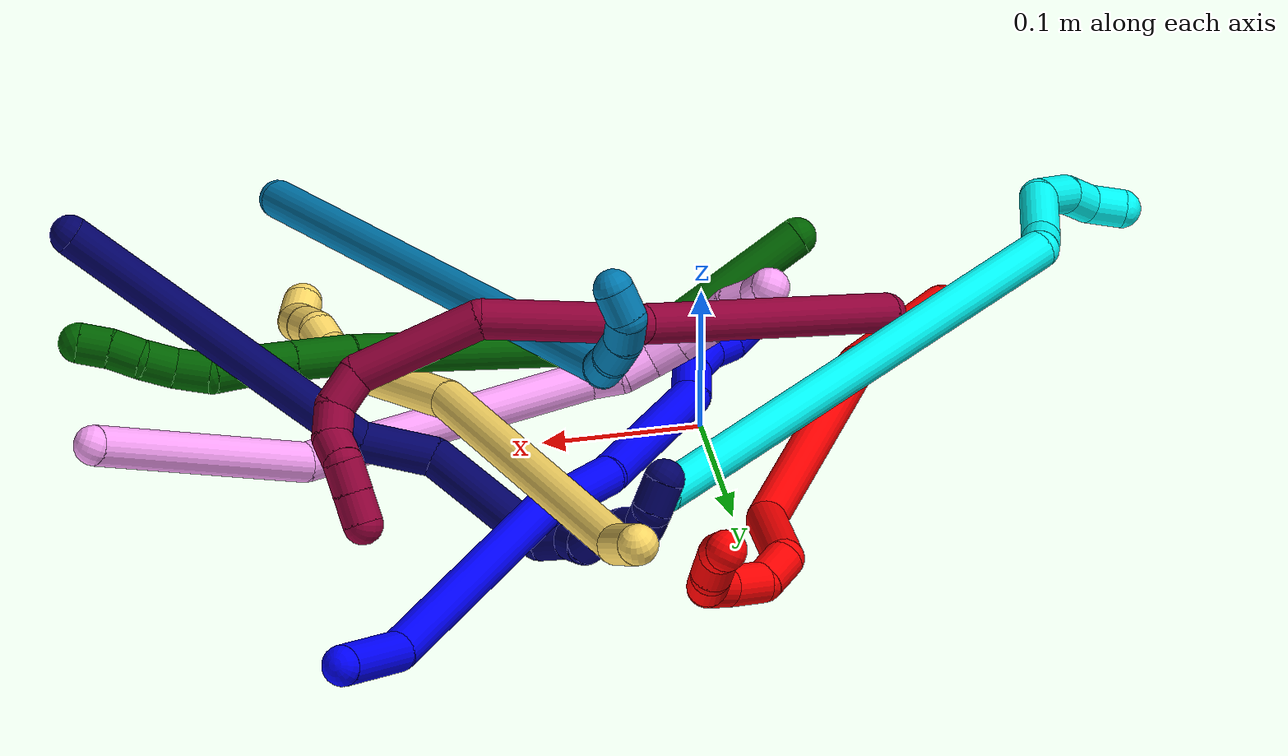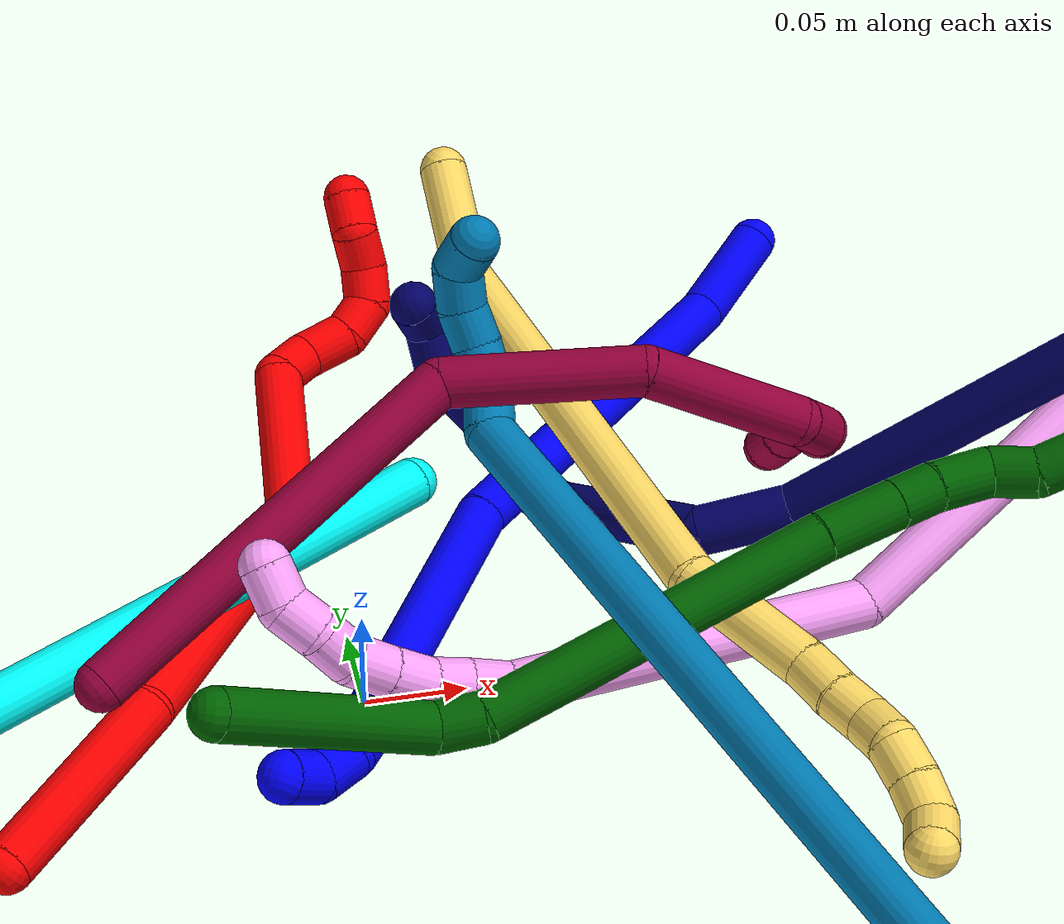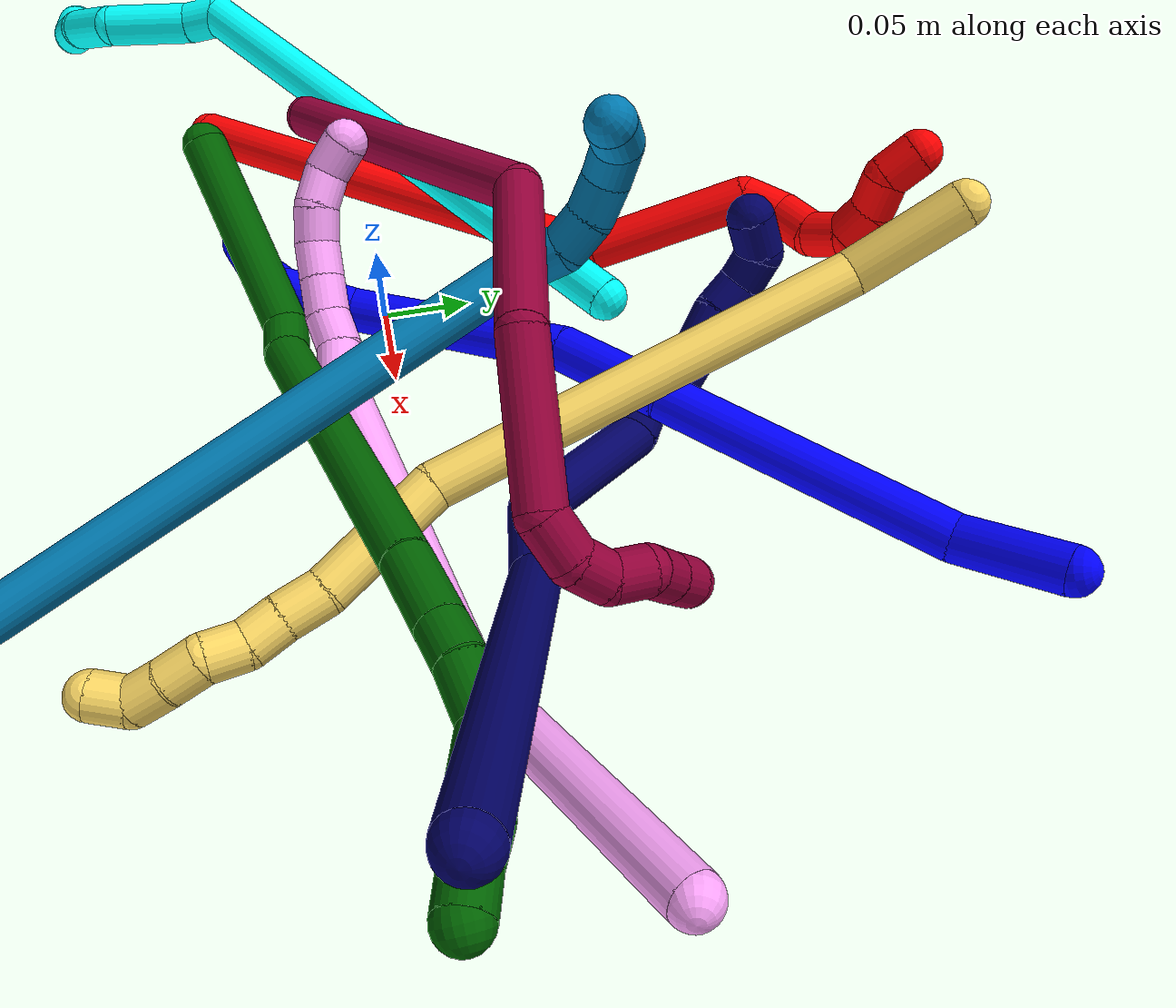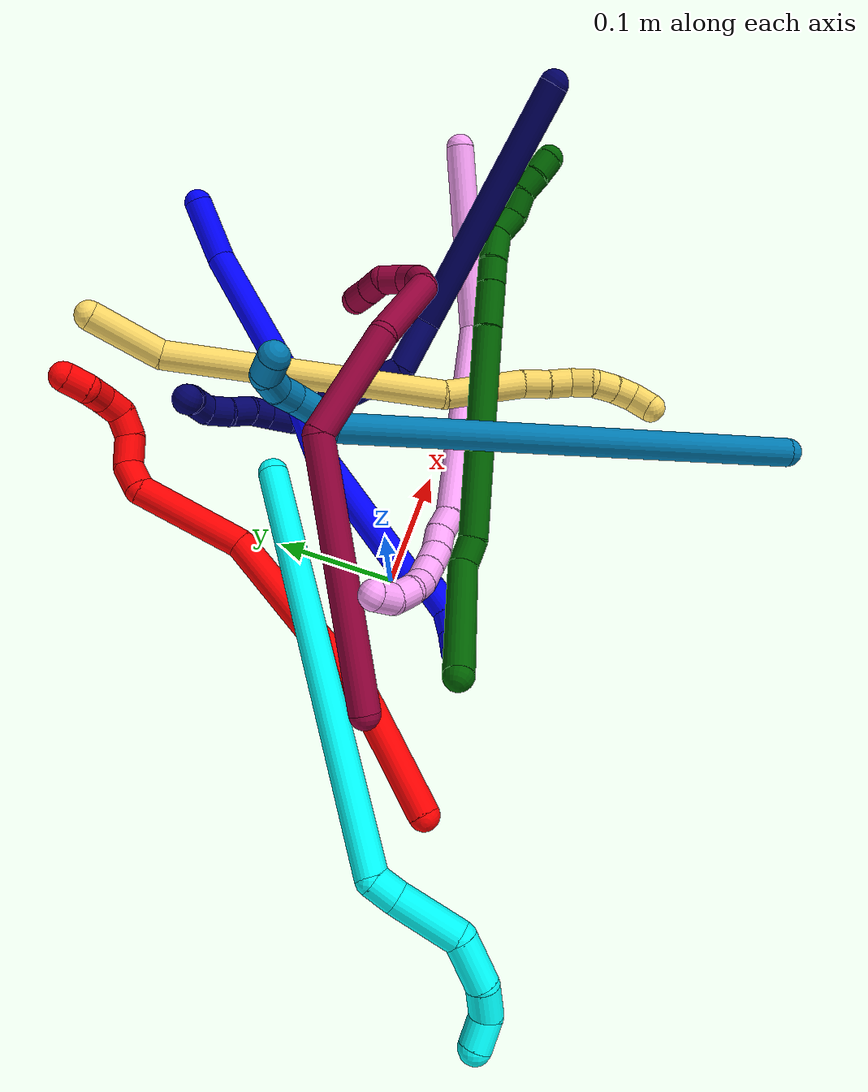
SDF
<sdf version="1.7">
 <world name="default">
  <plugin name="TubeGeneratorPlugin" filename="libtube_generator_plugin.so"/>
  <model name="photoneo_s_sensor">
   <static>1</static>
   <pose>0 0 2 1.57079 1.57079 3.14159</pose>
   <link name="link">
    <inertial><mass>0.1</mass></inertial>
    <sensor name="sensor" type="depth">
     <update_rate>30</update_rate>
     <camera>
      <horizontal_fov>1.22</horizontal_fov>
      <image><width>1920</width><height>1200</height><format>B8G8R8</format></image>
      <clip><near>0.1</near><far>4</far></clip>
      <depth_camera><output>points</output></depth_camera>
     </camera>
     <plugin name="camera_plugin" filename="libgazebo_ros_depth_camera.so">
      <baseline>0.2</baseline>
      <alwaysOn>1</alwaysOn>
      <updateRate>0.0</updateRate>
      <cameraName>camera_ir</cameraName>
      <imageTopicName>/camera/color/image_raw</imageTopicName>
      <cameraInfoTopicName>/camera/color/camera_info</cameraInfoTopicName>
      <depthImageTopicName>/camera/depth/image_raw</depthImageTopicName>
      <depthImageCameraInfoTopicName>/camera/depth/camera_info</depthImageCameraInfoTopicName>
      <pointCloudTopicName>/camera/depth/points</pointCloudTopicName>
      <frameName>fr_optical</frameName>
      <pointCloudCutoff>0.1</pointCloudCutoff>
      <pointCloudCutoffMax>2.0</pointCloudCutoffMax>
      <distortionK1>0</distortionK1>
      <distortionK2>0</distortionK2>
      <distortionK3>0</distortionK3>
      <distortionT1>0</distortionT1>
      <distortionT2>0</distortionT2>
      <CxPrime>0</CxPrime>
      <Cx>0</Cx>
      <Cy>0</Cy>
      <focalLength>0</focalLength>
      <hackBaseline>0</hackBaseline>
     </plugin>
    </sensor>
   </link>
  </model>
  <gravity>0 0 -9.8</gravity>
  <magnetic_field>6e-06 2.3e-05 -4.2e-05</magnetic_field>
  <atmosphere type="adiabatic"/>
  <physics name="default_physics" default="0" type="ode">
   <max_step_size>0.003</max_step_size>
   <real_time_factor>1</real_time_factor>
   <real_time_update_rate>1000</real_time_update_rate>
   <max_contacts>10000</max_contacts>
   <ode>
    <solver>
     <type>quick</type>
     <iters>100</iters>
     <sor>1.3</sor>
     <use_dynamic_moi_rescaling>0</use_dynamic_moi_rescaling>
    </solver>
    <constraints>
     <contact_max_correcting_vel>0</contact_max_correcting_vel>
     <contact_surface_layer>0.001</contact_surface_layer>
     <cfm>0</cfm>
     <erp>0.2</erp>
    </constraints>
   </ode>
  </physics>
  <scene><ambient>0.4 0.4 0.4 1</ambient><background>0.7 0.7 0.7 1</background><shadows>0</shadows></scene>
  <audio><device>default</device></audio>
  <spherical_coordinates>
   <surface_model>EARTH_WGS84</surface_model>
   <latitude_deg>0</latitude_deg>
   <longitude_deg>0</longitude_deg>
   <elevation>0</elevation>
   <heading_deg>0</heading_deg>
  </spherical_coordinates>
  <model name="bin">
   <static>1</static>
   <link name="bottom">
    <collision name="collision-bottom">
     <pose>0 0 -0.01 0 -0 0</pose>
     <geometry><box><size>0.8 0.6 0.02</size></box></geometry>
     <surface>
      <friction><ode><mu>100</mu><mu2>100</mu2></ode></friction>
      <contact><collide_bitmask>65535</collide_bitmask></contact>
     </surface>
    </collision>
   </link>
   <link name="west_wall">
    <collision name="collision-west_wall">
     <pose>-0.41 0 0.1 0 -0 0</pose>
     <geometry><box><size>0.02 0.6 0.2</size></box></geometry>
     <surface>
      <friction><ode><mu>100</mu><mu2>100</mu2></ode></friction>
      <contact><collide_bitmask>65535</collide_bitmask></contact>
     </surface>
    </collision>
   </link>
   <link name="east_wall">
    <collision name="collision-east_wall">
     <pose>0.41 0 0.1 0 -0 0</pose>
     <geometry><box><size>0.02 0.6 0.2</size></box></geometry>
     <surface>
      <friction><ode><mu>100</mu><mu2>100</mu2></ode></friction>
      <contact><collide_bitmask>65535</collide_bitmask></contact>
     </surface>
    </collision>
   </link>
   <link name="south_wall">
    <collision name="collision-south_wall">
     <pose>0 -0.31 0.1 0 -0 0</pose>
     <geometry><box><size>0.8 0.02 0.2</size></box></geometry>
     <surface>
      <friction><ode><mu>100</mu><mu2>100</mu2></ode></friction>
      <contact><collide_bitmask>65535</collide_bitmask></contact>
     </surface>
    </collision>
   </link>
   <link name="north_wall">
    <collision name="collision-north_wall">
     <pose>0 0.31 0.1 0 -0 0</pose>
     <geometry><box><size>0.8 0.02 0.2</size></box></geometry>
     <surface>
      <friction><ode><mu>100</mu><mu2>100</mu2></ode></friction>
      <contact><collide_bitmask>65535</collide_bitmask></contact>
     </surface>
    </collision>
   </link>
  </model>
  <model name="1">
   <static>0</static>
   <link name="1">
    <collision name="collision-cylinder-e_1_1_4">
     <pose>-0.008177 -0.003616 -0.026879 3.00788 -0.292852 -2.28922</pose>
     <geometry><cylinder><radius>0.0125</radius><length>0.056653</length></cylinder></geometry>
     <surface>
      <friction><ode><mu>1.16</mu><mu2>1.16</mu2><slip1>0</slip1><slip2>0</slip2></ode></friction>
      <contact><ode><kp>1e+06</kp><kd>1</kd><max_vel>0</max_vel><min_depth>0.001</min_depth></ode></contact>
     </surface>
    </collision>
    <visual name="visual-cylinder-e_1_1_4">
     <pose>-0.008177 -0.003616 -0.026879 3.00788 -0.292852 -2.28922</pose>
     <geometry><cylinder><radius>0.0125</radius><length>0.056653</length></cylinder></geometry>
     <material><ambient>0 0 1 1</ambient></material>
    </visual>
    <collision name="collision-cylinder-e_2_4_5">
     <pose>-0.048347 -0.046068 -0.116344 2.58622 -0.409757 -1.25982</pose>
     <geometry><cylinder><radius>0.0125</radius><length>0.16061</length></cylinder></geometry>
     <surface>
      <friction><ode><mu>1.16</mu><mu2>1.16</mu2><slip1>0</slip1><slip2>0</slip2></ode></friction>
      <contact><ode><kp>1e+06</kp><kd>1</kd><max_vel>0</max_vel><min_depth>0.001</min_depth></ode></contact>
     </surface>
    </collision>
    <visual name="visual-cylinder-e_2_4_5">
     <pose>-0.048347 -0.046068 -0.116344 2.58622 -0.409757 -1.25982</pose>
     <geometry><cylinder><radius>0.0125</radius><length>0.16061</length></cylinder></geometry>
     <material><ambient>0 0 1 1</ambient></material>
    </visual>
    <collision name="collision-cylinder-e_3_5_6">
     <pose>-0.094537 -0.094391 -0.206491 2.81005 -0.453282 -1.88631</pose>
     <geometry><cylinder><radius>0.0125</radius><length>0.064842</length></cylinder></geometry>
     <surface>
      <friction><ode><mu>1.16</mu><mu2>1.16</mu2><slip1>0</slip1><slip2>0</slip2></ode></friction>
      <contact><ode><kp>1e+06</kp><kd>1</kd><max_vel>0</max_vel><min_depth>0.001</min_depth></ode></contact>
     </surface>
    </collision>
    <visual name="visual-cylinder-e_3_5_6">
     <pose>-0.094537 -0.094391 -0.206491 2.81005 -0.453282 -1.88631</pose>
     <geometry><cylinder><radius>0.0125</radius><length>0.064842</length></cylinder></geometry>
     <material><ambient>0 0 1 1</ambient></material>
    </visual>
    <collision name="collision-cylinder-e_4_6_7">
     <pose>-0.121235 -0.130009 -0.29375 2.72901 -0.189502 -0.852573</pose>
     <geometry><cylinder><radius>0.0125</radius><length>0.132712</length></cylinder></geometry>
     <surface>
      <friction><ode><mu>1.16</mu><mu2>1.16</mu2><slip1>0</slip1><slip2>0</slip2></ode></friction>
      <contact><ode><kp>1e+06</kp><kd>1</kd><max_vel>0</max_vel><min_depth>0.001</min_depth></ode></contact>
     </surface>
    </collision>
    <visual name="visual-cylinder-e_4_6_7">
     <pose>-0.121235 -0.130009 -0.29375 2.72901 -0.189502 -0.852573</pose>
     <geometry><cylinder><radius>0.0125</radius><length>0.132712</length></cylinder></geometry>
     <material><ambient>0 0 1 1</ambient></material>
    </visual>
    <collision name="collision-cylinder-e_5_7_8">
     <pose>-0.134238 -0.165405 -0.358349 2.05722 -0.048012 -0.079673</pose>
     <geometry><cylinder><radius>0.0125</radius><length>0.020986</length></cylinder></geometry>
     <surface>
      <friction><ode><mu>1.16</mu><mu2>1.16</mu2><slip1>0</slip1><slip2>0</slip2></ode></friction>
      <contact><ode><kp>1e+06</kp><kd>1</kd><max_vel>0</max_vel><min_depth>0.001</min_depth></ode></contact>
     </surface>
    </collision>
    <visual name="visual-cylinder-e_5_7_8">
     <pose>-0.134238 -0.165405 -0.358349 2.05722 -0.048012 -0.079673</pose>
     <geometry><cylinder><radius>0.0125</radius><length>0.020986</length></cylinder></geometry>
     <material><ambient>0 0 1 1</ambient></material>
    </visual>
    <collision name="collision-cylinder-e_6_8_9">
     <pose>-0.137884 -0.180329 -0.373221 2.6255 -0.267513 -0.942956</pose>
     <geometry><cylinder><radius>0.0125</radius><length>0.023779</length></cylinder></geometry>
     <surface>
      <friction><ode><mu>1.16</mu><mu2>1.16</mu2><slip1>0</slip1><slip2>0</slip2></ode></friction>
      <contact><ode><kp>1e+06</kp><kd>1</kd><max_vel>0</max_vel><min_depth>0.001</min_depth></ode></contact>
     </surface>
    </collision>
    <visual name="visual-cylinder-e_6_8_9">
     <pose>-0.137884 -0.180329 -0.373221 2.6255 -0.267513 -0.942956</pose>
     <geometry><cylinder><radius>0.0125</radius><length>0.023779</length></cylinder></geometry>
     <material><ambient>0 0 1 1</ambient></material>
    </visual>
    <collision name="collision-cylinder-e_7_9_10">
     <pose>-0.146526 -0.188368 -0.391346 2.85746 -0.574695 -2.24009</pose>
     <geometry><cylinder><radius>0.0125</radius><length>0.020235</length></cylinder></geometry>
     <surface>
      <friction><ode><mu>1.16</mu><mu2>1.16</mu2><slip1>0</slip1><slip2>0</slip2></ode></friction>
      <contact><ode><kp>1e+06</kp><kd>1</kd><max_vel>0</max_vel><min_depth>0.001</min_depth></ode></contact>
     </surface>
    </collision>
    <visual name="visual-cylinder-e_7_9_10">
     <pose>-0.146526 -0.188368 -0.391346 2.85746 -0.574695 -2.24009</pose>
     <geometry><cylinder><radius>0.0125</radius><length>0.020235</length></cylinder></geometry>
     <material><ambient>0 0 1 1</ambient></material>
    </visual>
    <collision name="collision-cylinder-e_8_10_2">
     <pose>-0.159717 -0.19629 -0.402959 2.12913 -0.866619 -1.39078</pose>
     <geometry><cylinder><radius>0.0125</radius><length>0.020183</length></cylinder></geometry>
     <surface>
      <friction><ode><mu>1.16</mu><mu2>1.16</mu2><slip1>0</slip1><slip2>0</slip2></ode></friction>
      <contact><ode><kp>1e+06</kp><kd>1</kd><max_vel>0</max_vel><min_depth>0.001</min_depth></ode></contact>
     </surface>
    </collision>
    <visual name="visual-cylinder-e_8_10_2">
     <pose>-0.159717 -0.19629 -0.402959 2.12913 -0.866619 -1.39078</pose>
     <geometry><cylinder><radius>0.0125</radius><length>0.020183</length></cylinder></geometry>
     <material><ambient>0 0 1 1</ambient></material>
    </visual>
    <collision name="collision-sphere-2">
     <pose>-0.167409 -0.201831 -0.40642 0 -0 0</pose>
     <geometry><sphere><radius>0.0125</radius></sphere></geometry>
     <surface>
      <friction><ode><mu>1.16</mu><mu2>1.16</mu2><slip1>0</slip1><slip2>0</slip2></ode></friction>
      <contact><ode><kp>1e+06</kp><kd>1</kd><max_vel>0</max_vel><min_depth>0.001</min_depth></ode></contact>
     </surface>
    </collision>
    <visual name="visual-sphere-2">
     <pose>-0.167409 -0.201831 -0.40642 0 -0 0</pose>
     <geometry><sphere><radius>0.0125</radius></sphere></geometry>
     <material><ambient>0 0 1 1</ambient></material>
    </visual>
    <collision name="collision-sphere-10">
     <pose>-0.152026 -0.190748 -0.399498 0 -0 0</pose>
     <geometry><sphere><radius>0.0125</radius></sphere></geometry>
     <surface>
      <friction><ode><mu>1.16</mu><mu2>1.16</mu2><slip1>0</slip1><slip2>0</slip2></ode></friction>
      <contact><ode><kp>1e+06</kp><kd>1</kd><max_vel>0</max_vel><min_depth>0.001</min_depth></ode></contact>
     </surface>
    </collision>
    <visual name="visual-sphere-10">
     <pose>-0.152026 -0.190748 -0.399498 0 -0 0</pose>
     <geometry><sphere><radius>0.0125</radius></sphere></geometry>
     <material><ambient>0 0 1 1</ambient></material>
    </visual>
    <collision name="collision-sphere-9">
     <pose>-0.141027 -0.185987 -0.383195 0 -0 0</pose>
     <geometry><sphere><radius>0.0125</radius></sphere></geometry>
     <surface>
      <friction><ode><mu>1.16</mu><mu2>1.16</mu2><slip1>0</slip1><slip2>0</slip2></ode></friction>
      <contact><ode><kp>1e+06</kp><kd>1</kd><max_vel>0</max_vel><min_depth>0.001</min_depth></ode></contact>
     </surface>
    </collision>
    <visual name="visual-sphere-9">
     <pose>-0.141027 -0.185987 -0.383195 0 -0 0</pose>
     <geometry><sphere><radius>0.0125</radius></sphere></geometry>
     <material><ambient>0 0 1 1</ambient></material>
    </visual>
    <collision name="collision-sphere-4">
     <pose>-0.016355 -0.007231 -0.053757 0 -0 0</pose>
     <geometry><sphere><radius>0.0125</radius></sphere></geometry>
     <surface>
      <friction><ode><mu>1.16</mu><mu2>1.16</mu2><slip1>0</slip1><slip2>0</slip2></ode></friction>
      <contact><ode><kp>1e+06</kp><kd>1</kd><max_vel>0</max_vel><min_depth>0.001</min_depth></ode></contact>
     </surface>
    </collision>
    <visual name="visual-sphere-4">
     <pose>-0.016355 -0.007231 -0.053757 0 -0 0</pose>
     <geometry><sphere><radius>0.0125</radius></sphere></geometry>
     <material><ambient>0 0 1 1</ambient></material>
    </visual>
    <collision name="collision-sphere-1">
     <geometry><sphere><radius>0.0125</radius></sphere></geometry>
     <surface>
      <friction><ode><mu>1.16</mu><mu2>1.16</mu2><slip1>0</slip1><slip2>0</slip2></ode></friction>
      <contact><ode><kp>1e+06</kp><kd>1</kd><max_vel>0</max_vel><min_depth>0.001</min_depth></ode></contact>
     </surface>
    </collision>
    <visual name="visual-sphere-1">
     <geometry><sphere><radius>0.0125</radius></sphere></geometry>
     <material><ambient>0 0 1 1</ambient></material>
    </visual>
    <collision name="collision-sphere-8">
     <pose>-0.134741 -0.17467 -0.363248 0 -0 0</pose>
     <geometry><sphere><radius>0.0125</radius></sphere></geometry>
     <surface>
      <friction><ode><mu>1.16</mu><mu2>1.16</mu2><slip1>0</slip1><slip2>0</slip2></ode></friction>
      <contact><ode><kp>1e+06</kp><kd>1</kd><max_vel>0</max_vel><min_depth>0.001</min_depth></ode></contact>
     </surface>
    </collision>
    <visual name="visual-sphere-8">
     <pose>-0.134741 -0.17467 -0.363248 0 -0 0</pose>
     <geometry><sphere><radius>0.0125</radius></sphere></geometry>
     <material><ambient>0 0 1 1</ambient></material>
    </visual>
    <collision name="collision-sphere-5">
     <pose>-0.08034 -0.084904 -0.178931 0 -0 0</pose>
     <geometry><sphere><radius>0.0125</radius></sphere></geometry>
     <surface>
      <friction><ode><mu>1.16</mu><mu2>1.16</mu2><slip1>0</slip1><slip2>0</slip2></ode></friction>
      <contact><ode><kp>1e+06</kp><kd>1</kd><max_vel>0</max_vel><min_depth>0.001</min_depth></ode></contact>
     </surface>
    </collision>
    <visual name="visual-sphere-5">
     <pose>-0.08034 -0.084904 -0.178931 0 -0 0</pose>
     <geometry><sphere><radius>0.0125</radius></sphere></geometry>
     <material><ambient>0 0 1 1</ambient></material>
    </visual>
    <collision name="collision-sphere-6">
     <pose>-0.108735 -0.103879 -0.23405 0 -0 0</pose>
     <geometry><sphere><radius>0.0125</radius></sphere></geometry>
     <surface>
      <friction><ode><mu>1.16</mu><mu2>1.16</mu2><slip1>0</slip1><slip2>0</slip2></ode></friction>
      <contact><ode><kp>1e+06</kp><kd>1</kd><max_vel>0</max_vel><min_depth>0.001</min_depth></ode></contact>
     </surface>
    </collision>
    <visual name="visual-sphere-6">
     <pose>-0.108735 -0.103879 -0.23405 0 -0 0</pose>
     <geometry><sphere><radius>0.0125</radius></sphere></geometry>
     <material><ambient>0 0 1 1</ambient></material>
    </visual>
    <collision name="collision-sphere-7">
     <pose>-0.133734 -0.15614 -0.353449 0 -0 0</pose>
     <geometry><sphere><radius>0.0125</radius></sphere></geometry>
     <surface>
      <friction><ode><mu>1.16</mu><mu2>1.16</mu2><slip1>0</slip1><slip2>0</slip2></ode></friction>
      <contact><ode><kp>1e+06</kp><kd>1</kd><max_vel>0</max_vel><min_depth>0.001</min_depth></ode></contact>
     </surface>
    </collision>
    <visual name="visual-sphere-7">
     <pose>-0.133734 -0.15614 -0.353449 0 -0 0</pose>
     <geometry><sphere><radius>0.0125</radius></sphere></geometry>
     <material><ambient>0 0 1 1</ambient></material>
    </visual>
    <inertial>
     <pose>-0.085464 -0.093021 -0.210058 0 -0 0</pose>
     <mass>0.5</mass>
     <inertia>
      <ixx>-0.000294</ixx>
      <ixy>0</ixy>
      <ixz>0</ixz>
      <iyy>-0.000616</iyy>
      <iyz>0</iyz>
      <izz>0.000426</izz>
     </inertia>
    </inertial>
   </link>
   <pose>0.271951 0.286829 0.054566 -0.893345 0.380798 -0.316649</pose>
  </model>
  <model name="2">
   <static>0</static>
   <link name="2">
    <collision name="collision-cylinder-e_1_1_4">
     <pose>0.020639 0.041918 0.026023 -1.01521 0.3962 -0.222382</pose>
     <geometry><cylinder><radius>0.0125</radius><length>0.106963</length></cylinder></geometry>
     <surface>
      <friction><ode><mu>1.16</mu><mu2>1.16</mu2><slip1>0</slip1><slip2>0</slip2></ode></friction>
      <contact><ode><kp>1e+06</kp><kd>1</kd><max_vel>0</max_vel><min_depth>0.001</min_depth></ode></contact>
     </surface>
    </collision>
    <visual name="visual-cylinder-e_1_1_4">
     <pose>0.020639 0.041918 0.026023 -1.01521 0.3962 -0.222382</pose>
     <geometry><cylinder><radius>0.0125</radius><length>0.106963</length></cylinder></geometry>
     <material><ambient>1 0 0 1</ambient></material>
    </visual>
    <collision name="collision-cylinder-e_2_4_5">
     <pose>0.08618 0.13313 0.102124 -0.777509 0.568593 -0.238246</pose>
     <geometry><cylinder><radius>0.0125</radius><length>0.166779</length></cylinder></geometry>
     <surface>
      <friction><ode><mu>1.16</mu><mu2>1.16</mu2><slip1>0</slip1><slip2>0</slip2></ode></friction>
      <contact><ode><kp>1e+06</kp><kd>1</kd><max_vel>0</max_vel><min_depth>0.001</min_depth></ode></contact>
     </surface>
    </collision>
    <visual name="visual-cylinder-e_2_4_5">
     <pose>0.08618 0.13313 0.102124 -0.777509 0.568593 -0.238246</pose>
     <geometry><cylinder><radius>0.0125</radius><length>0.166779</length></cylinder></geometry>
     <material><ambient>1 0 0 1</ambient></material>
    </visual>
    <collision name="collision-cylinder-e_3_5_6">
     <pose>0.170591 0.206914 0.156373 -1.40211 1.00949 -0.872727</pose>
     <geometry><cylinder><radius>0.0125</radius><length>0.093343</length></cylinder></geometry>
     <surface>
      <friction><ode><mu>1.16</mu><mu2>1.16</mu2><slip1>0</slip1><slip2>0</slip2></ode></friction>
      <contact><ode><kp>1e+06</kp><kd>1</kd><max_vel>0</max_vel><min_depth>0.001</min_depth></ode></contact>
     </surface>
    </collision>
    <visual name="visual-cylinder-e_3_5_6">
     <pose>0.170591 0.206914 0.156373 -1.40211 1.00949 -0.872727</pose>
     <geometry><cylinder><radius>0.0125</radius><length>0.093343</length></cylinder></geometry>
     <material><ambient>1 0 0 1</ambient></material>
    </visual>
    <collision name="collision-cylinder-e_4_6_7">
     <pose>0.214965 0.239687 0.16857 -0.80116 0.399091 -0.170869</pose>
     <geometry><cylinder><radius>0.0125</radius><length>0.025035</length></cylinder></geometry>
     <surface>
      <friction><ode><mu>1.16</mu><mu2>1.16</mu2><slip1>0</slip1><slip2>0</slip2></ode></friction>
      <contact><ode><kp>1e+06</kp><kd>1</kd><max_vel>0</max_vel><min_depth>0.001</min_depth></ode></contact>
     </surface>
    </collision>
    <visual name="visual-cylinder-e_4_6_7">
     <pose>0.214965 0.239687 0.16857 -0.80116 0.399091 -0.170869</pose>
     <geometry><cylinder><radius>0.0125</radius><length>0.025035</length></cylinder></geometry>
     <material><ambient>1 0 0 1</ambient></material>
    </visual>
    <collision name="collision-cylinder-e_5_7_8">
     <pose>0.218683 0.259887 0.18207 -1.14022 -0.087178 0.055912</pose>
     <geometry><cylinder><radius>0.0125</radius><length>0.026329</length></cylinder></geometry>
     <surface>
      <friction><ode><mu>1.16</mu><mu2>1.16</mu2><slip1>0</slip1><slip2>0</slip2></ode></friction>
      <contact><ode><kp>1e+06</kp><kd>1</kd><max_vel>0</max_vel><min_depth>0.001</min_depth></ode></contact>
     </surface>
    </collision>
    <visual name="visual-cylinder-e_5_7_8">
     <pose>0.218683 0.259887 0.18207 -1.14022 -0.087178 0.055912</pose>
     <geometry><cylinder><radius>0.0125</radius><length>0.026329</length></cylinder></geometry>
     <material><ambient>1 0 0 1</ambient></material>
    </visual>
    <collision name="collision-cylinder-e_6_8_9">
     <pose>0.220641 0.281717 0.189249 -1.40045 0.299357 -0.252806</pose>
     <geometry><cylinder><radius>0.0125</radius><length>0.021053</length></cylinder></geometry>
     <surface>
      <friction><ode><mu>1.16</mu><mu2>1.16</mu2><slip1>0</slip1><slip2>0</slip2></ode></friction>
      <contact><ode><kp>1e+06</kp><kd>1</kd><max_vel>0</max_vel><min_depth>0.001</min_depth></ode></contact>
     </surface>
    </collision>
    <visual name="visual-cylinder-e_6_8_9">
     <pose>0.220641 0.281717 0.189249 -1.40045 0.299357 -0.252806</pose>
     <geometry><cylinder><radius>0.0125</radius><length>0.021053</length></cylinder></geometry>
     <material><ambient>1 0 0 1</ambient></material>
    </visual>
    <collision name="collision-cylinder-e_7_9_10">
     <pose>0.229999 0.298334 0.186585 -2.14833 0.663363 -1.13224</pose>
     <geometry><cylinder><radius>0.0125</radius><length>0.020312</length></cylinder></geometry>
     <surface>
      <friction><ode><mu>1.16</mu><mu2>1.16</mu2><slip1>0</slip1><slip2>0</slip2></ode></friction>
      <contact><ode><kp>1e+06</kp><kd>1</kd><max_vel>0</max_vel><min_depth>0.001</min_depth></ode></contact>
     </surface>
    </collision>
    <visual name="visual-cylinder-e_7_9_10">
     <pose>0.229999 0.298334 0.186585 -2.14833 0.663363 -1.13224</pose>
     <geometry><cylinder><radius>0.0125</radius><length>0.020312</length></cylinder></geometry>
     <material><ambient>1 0 0 1</ambient></material>
    </visual>
    <collision name="collision-cylinder-e_8_10_11">
     <pose>0.240359 0.310137 0.174617 -2.55071 0.42184 -1.22613</pose>
     <geometry><cylinder><radius>0.0125</radius><length>0.02006</length></cylinder></geometry>
     <surface>
      <friction><ode><mu>1.16</mu><mu2>1.16</mu2><slip1>0</slip1><slip2>0</slip2></ode></friction>
      <contact><ode><kp>1e+06</kp><kd>1</kd><max_vel>0</max_vel><min_depth>0.001</min_depth></ode></contact>
     </surface>
    </collision>
    <visual name="visual-cylinder-e_8_10_11">
     <pose>0.240359 0.310137 0.174617 -2.55071 0.42184 -1.22613</pose>
     <geometry><cylinder><radius>0.0125</radius><length>0.02006</length></cylinder></geometry>
     <material><ambient>1 0 0 1</ambient></material>
    </visual>
    <collision name="collision-cylinder-e_9_11_2">
     <pose>0.252441 0.320739 0.164303 -2.029 0.914829 -1.33922</pose>
     <geometry><cylinder><radius>0.0125</radius><length>0.020126</length></cylinder></geometry>
     <surface>
      <friction><ode><mu>1.16</mu><mu2>1.16</mu2><slip1>0</slip1><slip2>0</slip2></ode></friction>
      <contact><ode><kp>1e+06</kp><kd>1</kd><max_vel>0</max_vel><min_depth>0.001</min_depth></ode></contact>
     </surface>
    </collision>
    <visual name="visual-cylinder-e_9_11_2">
     <pose>0.252441 0.320739 0.164303 -2.029 0.914829 -1.33922</pose>
     <geometry><cylinder><radius>0.0125</radius><length>0.020126</length></cylinder></geometry>
     <material><ambient>1 0 0 1</ambient></material>
    </visual>
    <collision name="collision-sphere-2">
     <pose>0.260415 0.326244 0.161588 0 -0 0</pose>
     <geometry><sphere><radius>0.0125</radius></sphere></geometry>
     <surface>
      <friction><ode><mu>1.16</mu><mu2>1.16</mu2><slip1>0</slip1><slip2>0</slip2></ode></friction>
      <contact><ode><kp>1e+06</kp><kd>1</kd><max_vel>0</max_vel><min_depth>0.001</min_depth></ode></contact>
     </surface>
    </collision>
    <visual name="visual-sphere-2">
     <pose>0.260415 0.326244 0.161588 0 -0 0</pose>
     <geometry><sphere><radius>0.0125</radius></sphere></geometry>
     <material><ambient>1 0 0 1</ambient></material>
    </visual>
    <collision name="collision-sphere-11">
     <pose>0.244466 0.315235 0.167018 0 -0 0</pose>
     <geometry><sphere><radius>0.0125</radius></sphere></geometry>
     <surface>
      <friction><ode><mu>1.16</mu><mu2>1.16</mu2><slip1>0</slip1><slip2>0</slip2></ode></friction>
      <contact><ode><kp>1e+06</kp><kd>1</kd><max_vel>0</max_vel><min_depth>0.001</min_depth></ode></contact>
     </surface>
    </collision>
    <visual name="visual-sphere-11">
     <pose>0.244466 0.315235 0.167018 0 -0 0</pose>
     <geometry><sphere><radius>0.0125</radius></sphere></geometry>
     <material><ambient>1 0 0 1</ambient></material>
    </visual>
    <collision name="collision-sphere-10">
     <pose>0.236253 0.305039 0.182216 0 -0 0</pose>
     <geometry><sphere><radius>0.0125</radius></sphere></geometry>
     <surface>
      <friction><ode><mu>1.16</mu><mu2>1.16</mu2><slip1>0</slip1><slip2>0</slip2></ode></friction>
      <contact><ode><kp>1e+06</kp><kd>1</kd><max_vel>0</max_vel><min_depth>0.001</min_depth></ode></contact>
     </surface>
    </collision>
    <visual name="visual-sphere-10">
     <pose>0.236253 0.305039 0.182216 0 -0 0</pose>
     <geometry><sphere><radius>0.0125</radius></sphere></geometry>
     <material><ambient>1 0 0 1</ambient></material>
    </visual>
    <collision name="collision-sphere-9">
     <pose>0.223745 0.29163 0.190954 0 -0 0</pose>
     <geometry><sphere><radius>0.0125</radius></sphere></geometry>
     <surface>
      <friction><ode><mu>1.16</mu><mu2>1.16</mu2><slip1>0</slip1><slip2>0</slip2></ode></friction>
      <contact><ode><kp>1e+06</kp><kd>1</kd><max_vel>0</max_vel><min_depth>0.001</min_depth></ode></contact>
     </surface>
    </collision>
    <visual name="visual-sphere-9">
     <pose>0.223745 0.29163 0.190954 0 -0 0</pose>
     <geometry><sphere><radius>0.0125</radius></sphere></geometry>
     <material><ambient>1 0 0 1</ambient></material>
    </visual>
    <collision name="collision-sphere-4">
     <pose>0.041279 0.083836 0.052046 0 -0 0</pose>
     <geometry><sphere><radius>0.0125</radius></sphere></geometry>
     <surface>
      <friction><ode><mu>1.16</mu><mu2>1.16</mu2><slip1>0</slip1><slip2>0</slip2></ode></friction>
      <contact><ode><kp>1e+06</kp><kd>1</kd><max_vel>0</max_vel><min_depth>0.001</min_depth></ode></contact>
     </surface>
    </collision>
    <visual name="visual-sphere-4">
     <pose>0.041279 0.083836 0.052046 0 -0 0</pose>
     <geometry><sphere><radius>0.0125</radius></sphere></geometry>
     <material><ambient>1 0 0 1</ambient></material>
    </visual>
    <collision name="collision-sphere-1">
     <geometry><sphere><radius>0.0125</radius></sphere></geometry>
     <surface>
      <friction><ode><mu>1.16</mu><mu2>1.16</mu2><slip1>0</slip1><slip2>0</slip2></ode></friction>
      <contact><ode><kp>1e+06</kp><kd>1</kd><max_vel>0</max_vel><min_depth>0.001</min_depth></ode></contact>
     </surface>
    </collision>
    <visual name="visual-sphere-1">
     <geometry><sphere><radius>0.0125</radius></sphere></geometry>
     <material><ambient>1 0 0 1</ambient></material>
    </visual>
    <collision name="collision-sphere-8">
     <pose>0.217536 0.271805 0.187544 0 -0 0</pose>
     <geometry><sphere><radius>0.0125</radius></sphere></geometry>
     <surface>
      <friction><ode><mu>1.16</mu><mu2>1.16</mu2><slip1>0</slip1><slip2>0</slip2></ode></friction>
      <contact><ode><kp>1e+06</kp><kd>1</kd><max_vel>0</max_vel><min_depth>0.001</min_depth></ode></contact>
     </surface>
    </collision>
    <visual name="visual-sphere-8">
     <pose>0.217536 0.271805 0.187544 0 -0 0</pose>
     <geometry><sphere><radius>0.0125</radius></sphere></geometry>
     <material><ambient>1 0 0 1</ambient></material>
    </visual>
    <collision name="collision-sphere-5">
     <pose>0.13108 0.182424 0.152202 0 -0 0</pose>
     <geometry><sphere><radius>0.0125</radius></sphere></geometry>
     <surface>
      <friction><ode><mu>1.16</mu><mu2>1.16</mu2><slip1>0</slip1><slip2>0</slip2></ode></friction>
      <contact><ode><kp>1e+06</kp><kd>1</kd><max_vel>0</max_vel><min_depth>0.001</min_depth></ode></contact>
     </surface>
    </collision>
    <visual name="visual-sphere-5">
     <pose>0.13108 0.182424 0.152202 0 -0 0</pose>
     <geometry><sphere><radius>0.0125</radius></sphere></geometry>
     <material><ambient>1 0 0 1</ambient></material>
    </visual>
    <collision name="collision-sphere-6">
     <pose>0.210101 0.231404 0.160544 0 -0 0</pose>
     <geometry><sphere><radius>0.0125</radius></sphere></geometry>
     <surface>
      <friction><ode><mu>1.16</mu><mu2>1.16</mu2><slip1>0</slip1><slip2>0</slip2></ode></friction>
      <contact><ode><kp>1e+06</kp><kd>1</kd><max_vel>0</max_vel><min_depth>0.001</min_depth></ode></contact>
     </surface>
    </collision>
    <visual name="visual-sphere-6">
     <pose>0.210101 0.231404 0.160544 0 -0 0</pose>
     <geometry><sphere><radius>0.0125</radius></sphere></geometry>
     <material><ambient>1 0 0 1</ambient></material>
    </visual>
    <collision name="collision-sphere-7">
     <pose>0.219829 0.24797 0.176596 0 -0 0</pose>
     <geometry><sphere><radius>0.0125</radius></sphere></geometry>
     <surface>
      <friction><ode><mu>1.16</mu><mu2>1.16</mu2><slip1>0</slip1><slip2>0</slip2></ode></friction>
      <contact><ode><kp>1e+06</kp><kd>1</kd><max_vel>0</max_vel><min_depth>0.001</min_depth></ode></contact>
     </surface>
    </collision>
    <visual name="visual-sphere-7">
     <pose>0.219829 0.24797 0.176596 0 -0 0</pose>
     <geometry><sphere><radius>0.0125</radius></sphere></geometry>
     <material><ambient>1 0 0 1</ambient></material>
    </visual>
    <inertial>
     <pose>0.125725 0.167023 0.116019 0 -0 0</pose>
     <mass>0.5</mass>
     <inertia>
      <ixx>0.000337</ixx>
      <ixy>0</ixy>
      <ixz>0</ixz>
      <iyy>0.00032</iyy>
      <iyz>0</iyz>
      <izz>-0.000665</izz>
     </inertia>
    </inertial>
   </link>
   <pose>-0.173597 -0.091282 0.011487 2.49207 -0.109748 2.01128</pose>
  </model>
  <model name="3">
   <static>0</static>
   <link name="3">
    <collision name="collision-cylinder-e_1_1_4">
     <pose>-0.159743 -0.045144 -0.037038 2.25788 -1.22034 -1.95191</pose>
     <geometry><cylinder><radius>0.0125</radius><length>0.340162</length></cylinder></geometry>
     <surface>
      <friction><ode><mu>1.16</mu><mu2>1.16</mu2><slip1>0</slip1><slip2>0</slip2></ode></friction>
      <contact><ode><kp>1e+06</kp><kd>1</kd><max_vel>0</max_vel><min_depth>0.001</min_depth></ode></contact>
     </surface>
    </collision>
    <visual name="visual-cylinder-e_1_1_4">
     <pose>-0.159743 -0.045144 -0.037038 2.25788 -1.22034 -1.95191</pose>
     <geometry><cylinder><radius>0.0125</radius><length>0.340162</length></cylinder></geometry>
     <material><ambient>0.003922 1 0.996078 1</ambient></material>
    </visual>
    <collision name="collision-cylinder-e_2_4_5">
     <pose>-0.326007 -0.090125 -0.083005 -3.12329 -0.630838 3.0855</pose>
     <geometry><cylinder><radius>0.0125</radius><length>0.022116</length></cylinder></geometry>
     <surface>
      <friction><ode><mu>1.16</mu><mu2>1.16</mu2><slip1>0</slip1><slip2>0</slip2></ode></friction>
      <contact><ode><kp>1e+06</kp><kd>1</kd><max_vel>0</max_vel><min_depth>0.001</min_depth></ode></contact>
     </surface>
    </collision>
    <visual name="visual-cylinder-e_2_4_5">
     <pose>-0.326007 -0.090125 -0.083005 -3.12329 -0.630838 3.0855</pose>
     <geometry><cylinder><radius>0.0125</radius><length>0.022116</length></cylinder></geometry>
     <material><ambient>0.003922 1 0.996078 1</ambient></material>
    </visual>
    <collision name="collision-cylinder-e_3_5_6">
     <pose>-0.345838 -0.095745 -0.1135 2.87961 -0.537469 -2.24919</pose>
     <geometry><cylinder><radius>0.0125</radius><length>0.051988</length></cylinder></geometry>
     <surface>
      <friction><ode><mu>1.16</mu><mu2>1.16</mu2><slip1>0</slip1><slip2>0</slip2></ode></friction>
      <contact><ode><kp>1e+06</kp><kd>1</kd><max_vel>0</max_vel><min_depth>0.001</min_depth></ode></contact>
     </surface>
    </collision>
    <visual name="visual-cylinder-e_3_5_6">
     <pose>-0.345838 -0.095745 -0.1135 2.87961 -0.537469 -2.24919</pose>
     <geometry><cylinder><radius>0.0125</radius><length>0.051988</length></cylinder></geometry>
     <material><ambient>0.003922 1 0.996078 1</ambient></material>
    </visual>
    <collision name="collision-cylinder-e_4_6_7">
     <pose>-0.375362 -0.098195 -0.143743 -2.77485 -1.05041 2.52213</pose>
     <geometry><cylinder><radius>0.0125</radius><length>0.037383</length></cylinder></geometry>
     <surface>
      <friction><ode><mu>1.16</mu><mu2>1.16</mu2><slip1>0</slip1><slip2>0</slip2></ode></friction>
      <contact><ode><kp>1e+06</kp><kd>1</kd><max_vel>0</max_vel><min_depth>0.001</min_depth></ode></contact>
     </surface>
    </collision>
    <visual name="visual-cylinder-e_4_6_7">
     <pose>-0.375362 -0.098195 -0.143743 -2.77485 -1.05041 2.52213</pose>
     <geometry><cylinder><radius>0.0125</radius><length>0.037383</length></cylinder></geometry>
     <material><ambient>0.003922 1 0.996078 1</ambient></material>
    </visual>
    <collision name="collision-cylinder-e_5_7_8">
     <pose>-0.402612 -0.089337 -0.155088 -2.0208 -1.06318 1.50591</pose>
     <geometry><cylinder><radius>0.0125</radius><length>0.025248</length></cylinder></geometry>
     <surface>
      <friction><ode><mu>1.16</mu><mu2>1.16</mu2><slip1>0</slip1><slip2>0</slip2></ode></friction>
      <contact><ode><kp>1e+06</kp><kd>1</kd><max_vel>0</max_vel><min_depth>0.001</min_depth></ode></contact>
     </surface>
    </collision>
    <visual name="visual-cylinder-e_5_7_8">
     <pose>-0.402612 -0.089337 -0.155088 -2.0208 -1.06318 1.50591</pose>
     <geometry><cylinder><radius>0.0125</radius><length>0.025248</length></cylinder></geometry>
     <material><ambient>0.003922 1 0.996078 1</ambient></material>
    </visual>
    <collision name="collision-cylinder-e_6_8_2">
     <pose>-0.424376 -0.081798 -0.153985 -0.490382 -1.1917 0.336135</pose>
     <geometry><cylinder><radius>0.0125</radius><length>0.023104</length></cylinder></geometry>
     <surface>
      <friction><ode><mu>1.16</mu><mu2>1.16</mu2><slip1>0</slip1><slip2>0</slip2></ode></friction>
      <contact><ode><kp>1e+06</kp><kd>1</kd><max_vel>0</max_vel><min_depth>0.001</min_depth></ode></contact>
     </surface>
    </collision>
    <visual name="visual-cylinder-e_6_8_2">
     <pose>-0.424376 -0.081798 -0.153985 -0.490382 -1.1917 0.336135</pose>
     <geometry><cylinder><radius>0.0125</radius><length>0.023104</length></cylinder></geometry>
     <material><ambient>0.003922 1 0.996078 1</ambient></material>
    </visual>
    <collision name="collision-sphere-2">
     <pose>-0.435107 -0.079785 -0.150214 0 -0 0</pose>
     <geometry><sphere><radius>0.0125</radius></sphere></geometry>
     <surface>
      <friction><ode><mu>1.16</mu><mu2>1.16</mu2><slip1>0</slip1><slip2>0</slip2></ode></friction>
      <contact><ode><kp>1e+06</kp><kd>1</kd><max_vel>0</max_vel><min_depth>0.001</min_depth></ode></contact>
     </surface>
    </collision>
    <visual name="visual-sphere-2">
     <pose>-0.435107 -0.079785 -0.150214 0 -0 0</pose>
     <geometry><sphere><radius>0.0125</radius></sphere></geometry>
     <material><ambient>0.003922 1 0.996078 1</ambient></material>
    </visual>
    <collision name="collision-sphere-4">
     <pose>-0.319485 -0.090288 -0.074077 0 -0 0</pose>
     <geometry><sphere><radius>0.0125</radius></sphere></geometry>
     <surface>
      <friction><ode><mu>1.16</mu><mu2>1.16</mu2><slip1>0</slip1><slip2>0</slip2></ode></friction>
      <contact><ode><kp>1e+06</kp><kd>1</kd><max_vel>0</max_vel><min_depth>0.001</min_depth></ode></contact>
     </surface>
    </collision>
    <visual name="visual-sphere-4">
     <pose>-0.319485 -0.090288 -0.074077 0 -0 0</pose>
     <geometry><sphere><radius>0.0125</radius></sphere></geometry>
     <material><ambient>0.003922 1 0.996078 1</ambient></material>
    </visual>
    <collision name="collision-sphere-1">
     <geometry><sphere><radius>0.0125</radius></sphere></geometry>
     <surface>
      <friction><ode><mu>1.16</mu><mu2>1.16</mu2><slip1>0</slip1><slip2>0</slip2></ode></friction>
      <contact><ode><kp>1e+06</kp><kd>1</kd><max_vel>0</max_vel><min_depth>0.001</min_depth></ode></contact>
     </surface>
    </collision>
    <visual name="visual-sphere-1">
     <geometry><sphere><radius>0.0125</radius></sphere></geometry>
     <material><ambient>0.003922 1 0.996078 1</ambient></material>
    </visual>
    <collision name="collision-sphere-8">
     <pose>-0.413644 -0.083811 -0.157757 0 -0 0</pose>
     <geometry><sphere><radius>0.0125</radius></sphere></geometry>
     <surface>
      <friction><ode><mu>1.16</mu><mu2>1.16</mu2><slip1>0</slip1><slip2>0</slip2></ode></friction>
      <contact><ode><kp>1e+06</kp><kd>1</kd><max_vel>0</max_vel><min_depth>0.001</min_depth></ode></contact>
     </surface>
    </collision>
    <visual name="visual-sphere-8">
     <pose>-0.413644 -0.083811 -0.157757 0 -0 0</pose>
     <geometry><sphere><radius>0.0125</radius></sphere></geometry>
     <material><ambient>0.003922 1 0.996078 1</ambient></material>
    </visual>
    <collision name="collision-sphere-5">
     <pose>-0.33253 -0.089961 -0.091933 0 -0 0</pose>
     <geometry><sphere><radius>0.0125</radius></sphere></geometry>
     <surface>
      <friction><ode><mu>1.16</mu><mu2>1.16</mu2><slip1>0</slip1><slip2>0</slip2></ode></friction>
      <contact><ode><kp>1e+06</kp><kd>1</kd><max_vel>0</max_vel><min_depth>0.001</min_depth></ode></contact>
     </surface>
    </collision>
    <visual name="visual-sphere-5">
     <pose>-0.33253 -0.089961 -0.091933 0 -0 0</pose>
     <geometry><sphere><radius>0.0125</radius></sphere></geometry>
     <material><ambient>0.003922 1 0.996078 1</ambient></material>
    </visual>
    <collision name="collision-sphere-6">
     <pose>-0.359145 -0.101528 -0.135067 0 -0 0</pose>
     <geometry><sphere><radius>0.0125</radius></sphere></geometry>
     <surface>
      <friction><ode><mu>1.16</mu><mu2>1.16</mu2><slip1>0</slip1><slip2>0</slip2></ode></friction>
      <contact><ode><kp>1e+06</kp><kd>1</kd><max_vel>0</max_vel><min_depth>0.001</min_depth></ode></contact>
     </surface>
    </collision>
    <visual name="visual-sphere-6">
     <pose>-0.359145 -0.101528 -0.135067 0 -0 0</pose>
     <geometry><sphere><radius>0.0125</radius></sphere></geometry>
     <material><ambient>0.003922 1 0.996078 1</ambient></material>
    </visual>
    <collision name="collision-sphere-7">
     <pose>-0.391579 -0.094863 -0.152418 0 -0 0</pose>
     <geometry><sphere><radius>0.0125</radius></sphere></geometry>
     <surface>
      <friction><ode><mu>1.16</mu><mu2>1.16</mu2><slip1>0</slip1><slip2>0</slip2></ode></friction>
      <contact><ode><kp>1e+06</kp><kd>1</kd><max_vel>0</max_vel><min_depth>0.001</min_depth></ode></contact>
     </surface>
    </collision>
    <visual name="visual-sphere-7">
     <pose>-0.391579 -0.094863 -0.152418 0 -0 0</pose>
     <geometry><sphere><radius>0.0125</radius></sphere></geometry>
     <material><ambient>0.003922 1 0.996078 1</ambient></material>
    </visual>
    <inertial>
     <pose>-0.227059 -0.060287 -0.066364 0 -0 0</pose>
     <mass>0.5</mass>
     <inertia>
      <ixx>-0.001521</ixx>
      <ixy>0</ixy>
      <ixz>0</ixz>
      <iyy>0.001955</iyy>
      <iyz>0</iyz>
      <izz>0.003973</izz>
     </inertia>
    </inertial>
   </link>
   <pose>0.046203 0.12087 0.037105 -1.35994 -0.162917 0.33762</pose>
  </model>
  <model name="4">
   <static>0</static>
   <link name="4">
    <collision name="collision-cylinder-e_1_1_4">
     <pose>-0.011018 -0.044413 -0.06943 2.57251 -0.132899 -0.447445</pose>
     <geometry><cylinder><radius>0.0125</radius><length>0.166306</length></cylinder></geometry>
     <surface>
      <friction><ode><mu>1.16</mu><mu2>1.16</mu2><slip1>0</slip1><slip2>0</slip2></ode></friction>
      <contact><ode><kp>1e+06</kp><kd>1</kd><max_vel>0</max_vel><min_depth>0.001</min_depth></ode></contact>
     </surface>
    </collision>
    <visual name="visual-cylinder-e_1_1_4">
     <pose>-0.011018 -0.044413 -0.06943 2.57251 -0.132899 -0.447445</pose>
     <geometry><cylinder><radius>0.0125</radius><length>0.166306</length></cylinder></geometry>
     <material><ambient>1 0.65098 0.996078 1</ambient></material>
    </visual>
    <collision name="collision-cylinder-e_2_4_5">
     <pose>-0.074835 -0.109943 -0.215434 2.8725 -0.58664 -2.29891</pose>
     <geometry><cylinder><radius>0.0125</radius><length>0.190757</length></cylinder></geometry>
     <surface>
      <friction><ode><mu>1.16</mu><mu2>1.16</mu2><slip1>0</slip1><slip2>0</slip2></ode></friction>
      <contact><ode><kp>1e+06</kp><kd>1</kd><max_vel>0</max_vel><min_depth>0.001</min_depth></ode></contact>
     </surface>
    </collision>
    <visual name="visual-cylinder-e_2_4_5">
     <pose>-0.074835 -0.109943 -0.215434 2.8725 -0.58664 -2.29891</pose>
     <geometry><cylinder><radius>0.0125</radius><length>0.190757</length></cylinder></geometry>
     <material><ambient>1 0.65098 0.996078 1</ambient></material>
    </visual>
    <collision name="collision-cylinder-e_3_5_6">
     <pose>-0.133148 -0.129717 -0.300515 -2.98496 -0.569505 2.6177</pose>
     <geometry><cylinder><radius>0.0125</radius><length>0.020456</length></cylinder></geometry>
     <surface>
      <friction><ode><mu>1.16</mu><mu2>1.16</mu2><slip1>0</slip1><slip2>0</slip2></ode></friction>
      <contact><ode><kp>1e+06</kp><kd>1</kd><max_vel>0</max_vel><min_depth>0.001</min_depth></ode></contact>
     </surface>
    </collision>
    <visual name="visual-cylinder-e_3_5_6">
     <pose>-0.133148 -0.129717 -0.300515 -2.98496 -0.569505 2.6177</pose>
     <geometry><cylinder><radius>0.0125</radius><length>0.020456</length></cylinder></geometry>
     <material><ambient>1 0.65098 0.996078 1</ambient></material>
    </visual>
    <collision name="collision-cylinder-e_4_6_7">
     <pose>-0.146302 -0.129269 -0.315797 3.01006 -0.841043 -2.84914</pose>
     <geometry><cylinder><radius>0.0125</radius><length>0.020497</length></cylinder></geometry>
     <surface>
      <friction><ode><mu>1.16</mu><mu2>1.16</mu2><slip1>0</slip1><slip2>0</slip2></ode></friction>
      <contact><ode><kp>1e+06</kp><kd>1</kd><max_vel>0</max_vel><min_depth>0.001</min_depth></ode></contact>
     </surface>
    </collision>
    <visual name="visual-cylinder-e_4_6_7">
     <pose>-0.146302 -0.129269 -0.315797 3.01006 -0.841043 -2.84914</pose>
     <geometry><cylinder><radius>0.0125</radius><length>0.020497</length></cylinder></geometry>
     <material><ambient>1 0.65098 0.996078 1</ambient></material>
    </visual>
    <collision name="collision-cylinder-e_5_7_8">
     <pose>-0.16226 -0.128689 -0.328877 -2.91169 -0.909264 2.67766</pose>
     <geometry><cylinder><radius>0.0125</radius><length>0.021088</length></cylinder></geometry>
     <surface>
      <friction><ode><mu>1.16</mu><mu2>1.16</mu2><slip1>0</slip1><slip2>0</slip2></ode></friction>
      <contact><ode><kp>1e+06</kp><kd>1</kd><max_vel>0</max_vel><min_depth>0.001</min_depth></ode></contact>
     </surface>
    </collision>
    <visual name="visual-cylinder-e_5_7_8">
     <pose>-0.16226 -0.128689 -0.328877 -2.91169 -0.909264 2.67766</pose>
     <geometry><cylinder><radius>0.0125</radius><length>0.021088</length></cylinder></geometry>
     <material><ambient>1 0.65098 0.996078 1</ambient></material>
    </visual>
    <collision name="collision-cylinder-e_6_8_9">
     <pose>-0.178937 -0.125529 -0.341105 -2.86452 -0.935938 2.60324</pose>
     <geometry><cylinder><radius>0.0125</radius><length>0.02076</length></cylinder></geometry>
     <surface>
      <friction><ode><mu>1.16</mu><mu2>1.16</mu2><slip1>0</slip1><slip2>0</slip2></ode></friction>
      <contact><ode><kp>1e+06</kp><kd>1</kd><max_vel>0</max_vel><min_depth>0.001</min_depth></ode></contact>
     </surface>
    </collision>
    <visual name="visual-cylinder-e_6_8_9">
     <pose>-0.178937 -0.125529 -0.341105 -2.86452 -0.935938 2.60324</pose>
     <geometry><cylinder><radius>0.0125</radius><length>0.02076</length></cylinder></geometry>
     <material><ambient>1 0.65098 0.996078 1</ambient></material>
    </visual>
    <collision name="collision-cylinder-e_7_9_10">
     <pose>-0.195982 -0.119984 -0.350247 -2.26593 -1.04613 1.77776</pose>
     <geometry><cylinder><radius>0.0125</radius><length>0.020076</length></cylinder></geometry>
     <surface>
      <friction><ode><mu>1.16</mu><mu2>1.16</mu2><slip1>0</slip1><slip2>0</slip2></ode></friction>
      <contact><ode><kp>1e+06</kp><kd>1</kd><max_vel>0</max_vel><min_depth>0.001</min_depth></ode></contact>
     </surface>
    </collision>
    <visual name="visual-cylinder-e_7_9_10">
     <pose>-0.195982 -0.119984 -0.350247 -2.26593 -1.04613 1.77776</pose>
     <geometry><cylinder><radius>0.0125</radius><length>0.020076</length></cylinder></geometry>
     <material><ambient>1 0.65098 0.996078 1</ambient></material>
    </visual>
    <collision name="collision-cylinder-e_8_10_11">
     <pose>-0.21105 -0.110394 -0.358623 -2.30361 -0.691516 1.36022</pose>
     <geometry><cylinder><radius>0.0125</radius><length>0.02001</length></cylinder></geometry>
     <surface>
      <friction><ode><mu>1.16</mu><mu2>1.16</mu2><slip1>0</slip1><slip2>0</slip2></ode></friction>
      <contact><ode><kp>1e+06</kp><kd>1</kd><max_vel>0</max_vel><min_depth>0.001</min_depth></ode></contact>
     </surface>
    </collision>
    <visual name="visual-cylinder-e_8_10_11">
     <pose>-0.21105 -0.110394 -0.358623 -2.30361 -0.691516 1.36022</pose>
     <geometry><cylinder><radius>0.0125</radius><length>0.02001</length></cylinder></geometry>
     <material><ambient>1 0.65098 0.996078 1</ambient></material>
    </visual>
    <collision name="collision-cylinder-e_9_11_2">
     <pose>-0.222801 -0.096266 -0.364831 -1.69548 -0.565263 0.635826</pose>
     <geometry><cylinder><radius>0.0125</radius><length>0.020051</length></cylinder></geometry>
     <surface>
      <friction><ode><mu>1.16</mu><mu2>1.16</mu2><slip1>0</slip1><slip2>0</slip2></ode></friction>
      <contact><ode><kp>1e+06</kp><kd>1</kd><max_vel>0</max_vel><min_depth>0.001</min_depth></ode></contact>
     </surface>
    </collision>
    <visual name="visual-cylinder-e_9_11_2">
     <pose>-0.222801 -0.096266 -0.364831 -1.69548 -0.565263 0.635826</pose>
     <geometry><cylinder><radius>0.0125</radius><length>0.020051</length></cylinder></geometry>
     <material><ambient>1 0.65098 0.996078 1</ambient></material>
    </visual>
    <collision name="collision-sphere-2">
     <pose>-0.228171 -0.087865 -0.365884 0 -0 0</pose>
     <geometry><sphere><radius>0.0125</radius></sphere></geometry>
     <surface>
      <friction><ode><mu>1.16</mu><mu2>1.16</mu2><slip1>0</slip1><slip2>0</slip2></ode></friction>
      <contact><ode><kp>1e+06</kp><kd>1</kd><max_vel>0</max_vel><min_depth>0.001</min_depth></ode></contact>
     </surface>
    </collision>
    <visual name="visual-sphere-2">
     <pose>-0.228171 -0.087865 -0.365884 0 -0 0</pose>
     <geometry><sphere><radius>0.0125</radius></sphere></geometry>
     <material><ambient>1 0.65098 0.996078 1</ambient></material>
    </visual>
    <collision name="collision-sphere-11">
     <pose>-0.217431 -0.104666 -0.363778 0 -0 0</pose>
     <geometry><sphere><radius>0.0125</radius></sphere></geometry>
     <surface>
      <friction><ode><mu>1.16</mu><mu2>1.16</mu2><slip1>0</slip1><slip2>0</slip2></ode></friction>
      <contact><ode><kp>1e+06</kp><kd>1</kd><max_vel>0</max_vel><min_depth>0.001</min_depth></ode></contact>
     </surface>
    </collision>
    <visual name="visual-sphere-11">
     <pose>-0.217431 -0.104666 -0.363778 0 -0 0</pose>
     <geometry><sphere><radius>0.0125</radius></sphere></geometry>
     <material><ambient>1 0.65098 0.996078 1</ambient></material>
    </visual>
    <collision name="collision-sphere-10">
     <pose>-0.20467 -0.116122 -0.353467 0 -0 0</pose>
     <geometry><sphere><radius>0.0125</radius></sphere></geometry>
     <surface>
      <friction><ode><mu>1.16</mu><mu2>1.16</mu2><slip1>0</slip1><slip2>0</slip2></ode></friction>
      <contact><ode><kp>1e+06</kp><kd>1</kd><max_vel>0</max_vel><min_depth>0.001</min_depth></ode></contact>
     </surface>
    </collision>
    <visual name="visual-sphere-10">
     <pose>-0.20467 -0.116122 -0.353467 0 -0 0</pose>
     <geometry><sphere><radius>0.0125</radius></sphere></geometry>
     <material><ambient>1 0.65098 0.996078 1</ambient></material>
    </visual>
    <collision name="collision-sphere-9">
     <pose>-0.187295 -0.123845 -0.347026 0 -0 0</pose>
     <geometry><sphere><radius>0.0125</radius></sphere></geometry>
     <surface>
      <friction><ode><mu>1.16</mu><mu2>1.16</mu2><slip1>0</slip1><slip2>0</slip2></ode></friction>
      <contact><ode><kp>1e+06</kp><kd>1</kd><max_vel>0</max_vel><min_depth>0.001</min_depth></ode></contact>
     </surface>
    </collision>
    <visual name="visual-sphere-9">
     <pose>-0.187295 -0.123845 -0.347026 0 -0 0</pose>
     <geometry><sphere><radius>0.0125</radius></sphere></geometry>
     <material><ambient>1 0.65098 0.996078 1</ambient></material>
    </visual>
    <collision name="collision-sphere-4">
     <pose>-0.022037 -0.088825 -0.138861 0 -0 0</pose>
     <geometry><sphere><radius>0.0125</radius></sphere></geometry>
     <surface>
      <friction><ode><mu>1.16</mu><mu2>1.16</mu2><slip1>0</slip1><slip2>0</slip2></ode></friction>
      <contact><ode><kp>1e+06</kp><kd>1</kd><max_vel>0</max_vel><min_depth>0.001</min_depth></ode></contact>
     </surface>
    </collision>
    <visual name="visual-sphere-4">
     <pose>-0.022037 -0.088825 -0.138861 0 -0 0</pose>
     <geometry><sphere><radius>0.0125</radius></sphere></geometry>
     <material><ambient>1 0.65098 0.996078 1</ambient></material>
    </visual>
    <collision name="collision-sphere-1">
     <geometry><sphere><radius>0.0125</radius></sphere></geometry>
     <surface>
      <friction><ode><mu>1.16</mu><mu2>1.16</mu2><slip1>0</slip1><slip2>0</slip2></ode></friction>
      <contact><ode><kp>1e+06</kp><kd>1</kd><max_vel>0</max_vel><min_depth>0.001</min_depth></ode></contact>
     </surface>
    </collision>
    <visual name="visual-sphere-1">
     <geometry><sphere><radius>0.0125</radius></sphere></geometry>
     <material><ambient>1 0.65098 0.996078 1</ambient></material>
    </visual>
    <collision name="collision-sphere-8">
     <pose>-0.17058 -0.127213 -0.335184 0 -0 0</pose>
     <geometry><sphere><radius>0.0125</radius></sphere></geometry>
     <surface>
      <friction><ode><mu>1.16</mu><mu2>1.16</mu2><slip1>0</slip1><slip2>0</slip2></ode></friction>
      <contact><ode><kp>1e+06</kp><kd>1</kd><max_vel>0</max_vel><min_depth>0.001</min_depth></ode></contact>
     </surface>
    </collision>
    <visual name="visual-sphere-8">
     <pose>-0.17058 -0.127213 -0.335184 0 -0 0</pose>
     <geometry><sphere><radius>0.0125</radius></sphere></geometry>
     <material><ambient>1 0.65098 0.996078 1</ambient></material>
    </visual>
    <collision name="collision-sphere-5">
     <pose>-0.127633 -0.13106 -0.292007 0 -0 0</pose>
     <geometry><sphere><radius>0.0125</radius></sphere></geometry>
     <surface>
      <friction><ode><mu>1.16</mu><mu2>1.16</mu2><slip1>0</slip1><slip2>0</slip2></ode></friction>
      <contact><ode><kp>1e+06</kp><kd>1</kd><max_vel>0</max_vel><min_depth>0.001</min_depth></ode></contact>
     </surface>
    </collision>
    <visual name="visual-sphere-5">
     <pose>-0.127633 -0.13106 -0.292007 0 -0 0</pose>
     <geometry><sphere><radius>0.0125</radius></sphere></geometry>
     <material><ambient>1 0.65098 0.996078 1</ambient></material>
    </visual>
    <collision name="collision-sphere-6">
     <pose>-0.138664 -0.128373 -0.309023 0 -0 0</pose>
     <geometry><sphere><radius>0.0125</radius></sphere></geometry>
     <surface>
      <friction><ode><mu>1.16</mu><mu2>1.16</mu2><slip1>0</slip1><slip2>0</slip2></ode></friction>
      <contact><ode><kp>1e+06</kp><kd>1</kd><max_vel>0</max_vel><min_depth>0.001</min_depth></ode></contact>
     </surface>
    </collision>
    <visual name="visual-sphere-6">
     <pose>-0.138664 -0.128373 -0.309023 0 -0 0</pose>
     <geometry><sphere><radius>0.0125</radius></sphere></geometry>
     <material><ambient>1 0.65098 0.996078 1</ambient></material>
    </visual>
    <collision name="collision-sphere-7">
     <pose>-0.153941 -0.130165 -0.32257 0 -0 0</pose>
     <geometry><sphere><radius>0.0125</radius></sphere></geometry>
     <surface>
      <friction><ode><mu>1.16</mu><mu2>1.16</mu2><slip1>0</slip1><slip2>0</slip2></ode></friction>
      <contact><ode><kp>1e+06</kp><kd>1</kd><max_vel>0</max_vel><min_depth>0.001</min_depth></ode></contact>
     </surface>
    </collision>
    <visual name="visual-sphere-7">
     <pose>-0.153941 -0.130165 -0.32257 0 -0 0</pose>
     <geometry><sphere><radius>0.0125</radius></sphere></geometry>
     <material><ambient>1 0.65098 0.996078 1</ambient></material>
    </visual>
    <inertial>
     <pose>-0.083183 -0.091058 -0.201603 0 -0 0</pose>
     <mass>0.5</mass>
     <inertia>
      <ixx>-0.000524</ixx>
      <ixy>0</ixy>
      <ixz>0</ixz>
      <iyy>-0.00037</iyy>
      <iyz>0</iyz>
      <izz>0.00069</izz>
     </inertia>
    </inertial>
   </link>
   <pose>0.388499 0.071198 0.082272 0.746317 0.991647 0.610541</pose>
  </model>
  <model name="5">
   <static>0</static>
   <link name="5">
    <collision name="collision-cylinder-e_1_1_4">
     <pose>0.017972 -0.014933 0.021381 0.609666 0.603383 0.195204</pose>
     <geometry><cylinder><radius>0.0125</radius><length>0.063343</length></cylinder></geometry>
     <surface>
      <friction><ode><mu>1.16</mu><mu2>1.16</mu2><slip1>0</slip1><slip2>0</slip2></ode></friction>
      <contact><ode><kp>1e+06</kp><kd>1</kd><max_vel>0</max_vel><min_depth>0.001</min_depth></ode></contact>
     </surface>
    </collision>
    <visual name="visual-cylinder-e_1_1_4">
     <pose>0.017972 -0.014933 0.021381 0.609666 0.603383 0.195204</pose>
     <geometry><cylinder><radius>0.0125</radius><length>0.063343</length></cylinder></geometry>
     <material><ambient>1 0.858824 0.4 1</ambient></material>
    </visual>
    <collision name="collision-cylinder-e_2_4_5">
     <pose>0.115864 -0.113345 0.075742 1.19454 0.727484 0.506706</pose>
     <geometry><cylinder><radius>0.0125</radius><length>0.240366</length></cylinder></geometry>
     <surface>
      <friction><ode><mu>1.16</mu><mu2>1.16</mu2><slip1>0</slip1><slip2>0</slip2></ode></friction>
      <contact><ode><kp>1e+06</kp><kd>1</kd><max_vel>0</max_vel><min_depth>0.001</min_depth></ode></contact>
     </surface>
    </collision>
    <visual name="visual-cylinder-e_2_4_5">
     <pose>0.115864 -0.113345 0.075742 1.19454 0.727484 0.506706</pose>
     <geometry><cylinder><radius>0.0125</radius><length>0.240366</length></cylinder></geometry>
     <material><ambient>1 0.858824 0.4 1</ambient></material>
    </visual>
    <collision name="collision-cylinder-e_3_5_6">
     <pose>0.210156 -0.228835 0.116954 1.31909 0.410161 0.319809</pose>
     <geometry><cylinder><radius>0.0125</radius><length>0.072081</length></cylinder></geometry>
     <surface>
      <friction><ode><mu>1.16</mu><mu2>1.16</mu2><slip1>0</slip1><slip2>0</slip2></ode></friction>
      <contact><ode><kp>1e+06</kp><kd>1</kd><max_vel>0</max_vel><min_depth>0.001</min_depth></ode></contact>
     </surface>
    </collision>
    <visual name="visual-cylinder-e_3_5_6">
     <pose>0.210156 -0.228835 0.116954 1.31909 0.410161 0.319809</pose>
     <geometry><cylinder><radius>0.0125</radius><length>0.072081</length></cylinder></geometry>
     <material><ambient>1 0.858824 0.4 1</ambient></material>
    </visual>
    <collision name="collision-cylinder-e_4_6_7">
     <pose>0.231635 -0.270024 0.12758 1.31567 0.643035 0.503764</pose>
     <geometry><cylinder><radius>0.0125</radius><length>0.023709</length></cylinder></geometry>
     <surface>
      <friction><ode><mu>1.16</mu><mu2>1.16</mu2><slip1>0</slip1><slip2>0</slip2></ode></friction>
      <contact><ode><kp>1e+06</kp><kd>1</kd><max_vel>0</max_vel><min_depth>0.001</min_depth></ode></contact>
     </surface>
    </collision>
    <visual name="visual-cylinder-e_4_6_7">
     <pose>0.231635 -0.270024 0.12758 1.31567 0.643035 0.503764</pose>
     <geometry><cylinder><radius>0.0125</radius><length>0.023709</length></cylinder></geometry>
     <material><ambient>1 0.858824 0.4 1</ambient></material>
    </visual>
    <collision name="collision-cylinder-e_5_7_8">
     <pose>0.243871 -0.287673 0.131828 1.35532 0.534087 0.433435</pose>
     <geometry><cylinder><radius>0.0125</radius><length>0.020144</length></cylinder></geometry>
     <surface>
      <friction><ode><mu>1.16</mu><mu2>1.16</mu2><slip1>0</slip1><slip2>0</slip2></ode></friction>
      <contact><ode><kp>1e+06</kp><kd>1</kd><max_vel>0</max_vel><min_depth>0.001</min_depth></ode></contact>
     </surface>
    </collision>
    <visual name="visual-cylinder-e_5_7_8">
     <pose>0.243871 -0.287673 0.131828 1.35532 0.534087 0.433435</pose>
     <geometry><cylinder><radius>0.0125</radius><length>0.020144</length></cylinder></geometry>
     <material><ambient>1 0.858824 0.4 1</ambient></material>
    </visual>
    <collision name="collision-cylinder-e_6_8_9">
     <pose>0.256672 -0.302812 0.133859 1.54424 0.85506 0.835194</pose>
     <geometry><cylinder><radius>0.0125</radius><length>0.02034</length></cylinder></geometry>
     <surface>
      <friction><ode><mu>1.16</mu><mu2>1.16</mu2><slip1>0</slip1><slip2>0</slip2></ode></friction>
      <contact><ode><kp>1e+06</kp><kd>1</kd><max_vel>0</max_vel><min_depth>0.001</min_depth></ode></contact>
     </surface>
    </collision>
    <visual name="visual-cylinder-e_6_8_9">
     <pose>0.256672 -0.302812 0.133859 1.54424 0.85506 0.835194</pose>
     <geometry><cylinder><radius>0.0125</radius><length>0.02034</length></cylinder></geometry>
     <material><ambient>1 0.858824 0.4 1</ambient></material>
    </visual>
    <collision name="collision-cylinder-e_7_9_10">
     <pose>0.270219 -0.316116 0.138678 0.960222 0.627523 0.334785</pose>
     <geometry><cylinder><radius>0.0125</radius><length>0.020003</length></cylinder></geometry>
     <surface>
      <friction><ode><mu>1.16</mu><mu2>1.16</mu2><slip1>0</slip1><slip2>0</slip2></ode></friction>
      <contact><ode><kp>1e+06</kp><kd>1</kd><max_vel>0</max_vel><min_depth>0.001</min_depth></ode></contact>
     </surface>
    </collision>
    <visual name="visual-cylinder-e_7_9_10">
     <pose>0.270219 -0.316116 0.138678 0.960222 0.627523 0.334785</pose>
     <geometry><cylinder><radius>0.0125</radius><length>0.020003</length></cylinder></geometry>
     <material><ambient>1 0.858824 0.4 1</ambient></material>
    </visual>
    <collision name="collision-cylinder-e_8_10_11">
     <pose>0.282247 -0.328514 0.148703 0.819538 0.662678 0.296661</pose>
     <geometry><cylinder><radius>0.0125</radius><length>0.020011</length></cylinder></geometry>
     <surface>
      <friction><ode><mu>1.16</mu><mu2>1.16</mu2><slip1>0</slip1><slip2>0</slip2></ode></friction>
      <contact><ode><kp>1e+06</kp><kd>1</kd><max_vel>0</max_vel><min_depth>0.001</min_depth></ode></contact>
     </surface>
    </collision>
    <visual name="visual-cylinder-e_8_10_11">
     <pose>0.282247 -0.328514 0.148703 0.819538 0.662678 0.296661</pose>
     <geometry><cylinder><radius>0.0125</radius><length>0.020011</length></cylinder></geometry>
     <material><ambient>1 0.858824 0.4 1</ambient></material>
    </visual>
    <collision name="collision-cylinder-e_9_11_2">
     <pose>0.298165 -0.335908 0.155528 0.846834 1.35159 0.693449</pose>
     <geometry><cylinder><radius>0.0125</radius><length>0.020004</length></cylinder></geometry>
     <surface>
      <friction><ode><mu>1.16</mu><mu2>1.16</mu2><slip1>0</slip1><slip2>0</slip2></ode></friction>
      <contact><ode><kp>1e+06</kp><kd>1</kd><max_vel>0</max_vel><min_depth>0.001</min_depth></ode></contact>
     </surface>
    </collision>
    <visual name="visual-cylinder-e_9_11_2">
     <pose>0.298165 -0.335908 0.155528 0.846834 1.35159 0.693449</pose>
     <geometry><cylinder><radius>0.0125</radius><length>0.020004</length></cylinder></geometry>
     <material><ambient>1 0.858824 0.4 1</ambient></material>
    </visual>
    <collision name="collision-sphere-2">
     <pose>0.307928 -0.337538 0.156968 0 -0 0</pose>
     <geometry><sphere><radius>0.0125</radius></sphere></geometry>
     <surface>
      <friction><ode><mu>1.16</mu><mu2>1.16</mu2><slip1>0</slip1><slip2>0</slip2></ode></friction>
      <contact><ode><kp>1e+06</kp><kd>1</kd><max_vel>0</max_vel><min_depth>0.001</min_depth></ode></contact>
     </surface>
    </collision>
    <visual name="visual-sphere-2">
     <pose>0.307928 -0.337538 0.156968 0 -0 0</pose>
     <geometry><sphere><radius>0.0125</radius></sphere></geometry>
     <material><ambient>1 0.858824 0.4 1</ambient></material>
    </visual>
    <collision name="collision-sphere-11">
     <pose>0.288402 -0.334279 0.154087 0 -0 0</pose>
     <geometry><sphere><radius>0.0125</radius></sphere></geometry>
     <surface>
      <friction><ode><mu>1.16</mu><mu2>1.16</mu2><slip1>0</slip1><slip2>0</slip2></ode></friction>
      <contact><ode><kp>1e+06</kp><kd>1</kd><max_vel>0</max_vel><min_depth>0.001</min_depth></ode></contact>
     </surface>
    </collision>
    <visual name="visual-sphere-11">
     <pose>0.288402 -0.334279 0.154087 0 -0 0</pose>
     <geometry><sphere><radius>0.0125</radius></sphere></geometry>
     <material><ambient>1 0.858824 0.4 1</ambient></material>
    </visual>
    <collision name="collision-sphere-10">
     <pose>0.276091 -0.32275 0.14332 0 -0 0</pose>
     <geometry><sphere><radius>0.0125</radius></sphere></geometry>
     <surface>
      <friction><ode><mu>1.16</mu><mu2>1.16</mu2><slip1>0</slip1><slip2>0</slip2></ode></friction>
      <contact><ode><kp>1e+06</kp><kd>1</kd><max_vel>0</max_vel><min_depth>0.001</min_depth></ode></contact>
     </surface>
    </collision>
    <visual name="visual-sphere-10">
     <pose>0.276091 -0.32275 0.14332 0 -0 0</pose>
     <geometry><sphere><radius>0.0125</radius></sphere></geometry>
     <material><ambient>1 0.858824 0.4 1</ambient></material>
    </visual>
    <collision name="collision-sphere-9">
     <pose>0.264347 -0.309483 0.134036 0 -0 0</pose>
     <geometry><sphere><radius>0.0125</radius></sphere></geometry>
     <surface>
      <friction><ode><mu>1.16</mu><mu2>1.16</mu2><slip1>0</slip1><slip2>0</slip2></ode></friction>
      <contact><ode><kp>1e+06</kp><kd>1</kd><max_vel>0</max_vel><min_depth>0.001</min_depth></ode></contact>
     </surface>
    </collision>
    <visual name="visual-sphere-9">
     <pose>0.264347 -0.309483 0.134036 0 -0 0</pose>
     <geometry><sphere><radius>0.0125</radius></sphere></geometry>
     <material><ambient>1 0.858824 0.4 1</ambient></material>
    </visual>
    <collision name="collision-sphere-4">
     <pose>0.035943 -0.029865 0.042761 0 -0 0</pose>
     <geometry><sphere><radius>0.0125</radius></sphere></geometry>
     <surface>
      <friction><ode><mu>1.16</mu><mu2>1.16</mu2><slip1>0</slip1><slip2>0</slip2></ode></friction>
      <contact><ode><kp>1e+06</kp><kd>1</kd><max_vel>0</max_vel><min_depth>0.001</min_depth></ode></contact>
     </surface>
    </collision>
    <visual name="visual-sphere-4">
     <pose>0.035943 -0.029865 0.042761 0 -0 0</pose>
     <geometry><sphere><radius>0.0125</radius></sphere></geometry>
     <material><ambient>1 0.858824 0.4 1</ambient></material>
    </visual>
    <collision name="collision-sphere-1">
     <geometry><sphere><radius>0.0125</radius></sphere></geometry>
     <surface>
      <friction><ode><mu>1.16</mu><mu2>1.16</mu2><slip1>0</slip1><slip2>0</slip2></ode></friction>
      <contact><ode><kp>1e+06</kp><kd>1</kd><max_vel>0</max_vel><min_depth>0.001</min_depth></ode></contact>
     </surface>
    </collision>
    <visual name="visual-sphere-1">
     <geometry><sphere><radius>0.0125</radius></sphere></geometry>
     <material><ambient>1 0.858824 0.4 1</ambient></material>
    </visual>
    <collision name="collision-sphere-8">
     <pose>0.248998 -0.296141 0.133682 0 -0 0</pose>
     <geometry><sphere><radius>0.0125</radius></sphere></geometry>
     <surface>
      <friction><ode><mu>1.16</mu><mu2>1.16</mu2><slip1>0</slip1><slip2>0</slip2></ode></friction>
      <contact><ode><kp>1e+06</kp><kd>1</kd><max_vel>0</max_vel><min_depth>0.001</min_depth></ode></contact>
     </surface>
    </collision>
    <visual name="visual-sphere-8">
     <pose>0.248998 -0.296141 0.133682 0 -0 0</pose>
     <geometry><sphere><radius>0.0125</radius></sphere></geometry>
     <material><ambient>1 0.858824 0.4 1</ambient></material>
    </visual>
    <collision name="collision-sphere-5">
     <pose>0.195785 -0.196825 0.108723 0 -0 0</pose>
     <geometry><sphere><radius>0.0125</radius></sphere></geometry>
     <surface>
      <friction><ode><mu>1.16</mu><mu2>1.16</mu2><slip1>0</slip1><slip2>0</slip2></ode></friction>
      <contact><ode><kp>1e+06</kp><kd>1</kd><max_vel>0</max_vel><min_depth>0.001</min_depth></ode></contact>
     </surface>
    </collision>
    <visual name="visual-sphere-5">
     <pose>0.195785 -0.196825 0.108723 0 -0 0</pose>
     <geometry><sphere><radius>0.0125</radius></sphere></geometry>
     <material><ambient>1 0.858824 0.4 1</ambient></material>
    </visual>
    <collision name="collision-sphere-6">
     <pose>0.224527 -0.260844 0.125186 0 -0 0</pose>
     <geometry><sphere><radius>0.0125</radius></sphere></geometry>
     <surface>
      <friction><ode><mu>1.16</mu><mu2>1.16</mu2><slip1>0</slip1><slip2>0</slip2></ode></friction>
      <contact><ode><kp>1e+06</kp><kd>1</kd><max_vel>0</max_vel><min_depth>0.001</min_depth></ode></contact>
     </surface>
    </collision>
    <visual name="visual-sphere-6">
     <pose>0.224527 -0.260844 0.125186 0 -0 0</pose>
     <geometry><sphere><radius>0.0125</radius></sphere></geometry>
     <material><ambient>1 0.858824 0.4 1</ambient></material>
    </visual>
    <collision name="collision-sphere-7">
     <pose>0.238744 -0.279204 0.129974 0 -0 0</pose>
     <geometry><sphere><radius>0.0125</radius></sphere></geometry>
     <surface>
      <friction><ode><mu>1.16</mu><mu2>1.16</mu2><slip1>0</slip1><slip2>0</slip2></ode></friction>
      <contact><ode><kp>1e+06</kp><kd>1</kd><max_vel>0</max_vel><min_depth>0.001</min_depth></ode></contact>
     </surface>
    </collision>
    <visual name="visual-sphere-7">
     <pose>0.238744 -0.279204 0.129974 0 -0 0</pose>
     <geometry><sphere><radius>0.0125</radius></sphere></geometry>
     <material><ambient>1 0.858824 0.4 1</ambient></material>
    </visual>
    <inertial>
     <pose>0.153558 -0.165315 0.090508 0 -0 0</pose>
     <mass>0.5</mass>
     <inertia><ixx>0.00128</ixx><ixy>0</ixy><ixz>0</ixz><iyy>0.001177</iyy><iyz>0</iyz><izz>6.1e-05</izz></inertia>
    </inertial>
   </link>
   <pose>0.095726 0.288505 0.119392 3.06751 -0.232942 -2.05479</pose>
  </model>
  <model name="6">
   <static>0</static>
   <link name="6">
    <collision name="collision-cylinder-e_1_1_4">
     <pose>-0.00577 0.012099 -0.056625 -2.93109 -0.099313 0.87942</pose>
     <geometry><cylinder><radius>0.0125</radius><length>0.11638</length></cylinder></geometry>
     <surface>
      <friction><ode><mu>1.16</mu><mu2>1.16</mu2><slip1>0</slip1><slip2>0</slip2></ode></friction>
      <contact><ode><kp>1e+06</kp><kd>1</kd><max_vel>0</max_vel><min_depth>0.001</min_depth></ode></contact>
     </surface>
    </collision>
    <visual name="visual-cylinder-e_1_1_4">
     <pose>-0.00577 0.012099 -0.056625 -2.93109 -0.099313 0.87942</pose>
     <geometry><cylinder><radius>0.0125</radius><length>0.11638</length></cylinder></geometry>
     <material><ambient>0 0.392157 0.003922 1</ambient></material>
    </visual>
    <collision name="collision-cylinder-e_2_4_5">
     <pose>-0.005911 0.023276 -0.123942 3.05558 0.482969 2.79563</pose>
     <geometry><cylinder><radius>0.0125</radius><length>0.024235</length></cylinder></geometry>
     <surface>
      <friction><ode><mu>1.16</mu><mu2>1.16</mu2><slip1>0</slip1><slip2>0</slip2></ode></friction>
      <contact><ode><kp>1e+06</kp><kd>1</kd><max_vel>0</max_vel><min_depth>0.001</min_depth></ode></contact>
     </surface>
    </collision>
    <visual name="visual-cylinder-e_2_4_5">
     <pose>-0.005911 0.023276 -0.123942 3.05558 0.482969 2.79563</pose>
     <geometry><cylinder><radius>0.0125</radius><length>0.024235</length></cylinder></geometry>
     <material><ambient>0 0.392157 0.003922 1</ambient></material>
    </visual>
    <collision name="collision-cylinder-e_3_5_6">
     <pose>0.049972 0.041485 -0.208136 -2.88697 0.584545 -2.33714</pose>
     <geometry><cylinder><radius>0.0125</radius><length>0.182147</length></cylinder></geometry>
     <surface>
      <friction><ode><mu>1.16</mu><mu2>1.16</mu2><slip1>0</slip1><slip2>0</slip2></ode></friction>
      <contact><ode><kp>1e+06</kp><kd>1</kd><max_vel>0</max_vel><min_depth>0.001</min_depth></ode></contact>
     </surface>
    </collision>
    <visual name="visual-cylinder-e_3_5_6">
     <pose>0.049972 0.041485 -0.208136 -2.88697 0.584545 -2.33714</pose>
     <geometry><cylinder><radius>0.0125</radius><length>0.182147</length></cylinder></geometry>
     <material><ambient>0 0.392157 0.003922 1</ambient></material>
    </visual>
    <collision name="collision-cylinder-e_4_6_7">
     <pose>0.110033 0.064739 -0.298863 -2.90664 0.505638 -2.28456</pose>
     <geometry><cylinder><radius>0.0125</radius><length>0.040486</length></cylinder></geometry>
     <surface>
      <friction><ode><mu>1.16</mu><mu2>1.16</mu2><slip1>0</slip1><slip2>0</slip2></ode></friction>
      <contact><ode><kp>1e+06</kp><kd>1</kd><max_vel>0</max_vel><min_depth>0.001</min_depth></ode></contact>
     </surface>
    </collision>
    <visual name="visual-cylinder-e_4_6_7">
     <pose>0.110033 0.064739 -0.298863 -2.90664 0.505638 -2.28456</pose>
     <geometry><cylinder><radius>0.0125</radius><length>0.040486</length></cylinder></geometry>
     <material><ambient>0 0.392157 0.003922 1</ambient></material>
    </visual>
    <collision name="collision-cylinder-e_5_7_8">
     <pose>0.124955 0.071089 -0.325367 -2.90609 0.492158 -2.26126</pose>
     <geometry><cylinder><radius>0.0125</radius><length>0.021659</length></cylinder></geometry>
     <surface>
      <friction><ode><mu>1.16</mu><mu2>1.16</mu2><slip1>0</slip1><slip2>0</slip2></ode></friction>
      <contact><ode><kp>1e+06</kp><kd>1</kd><max_vel>0</max_vel><min_depth>0.001</min_depth></ode></contact>
     </surface>
    </collision>
    <visual name="visual-cylinder-e_5_7_8">
     <pose>0.124955 0.071089 -0.325367 -2.90609 0.492158 -2.26126</pose>
     <geometry><cylinder><radius>0.0125</radius><length>0.021659</length></cylinder></geometry>
     <material><ambient>0 0.392157 0.003922 1</ambient></material>
    </visual>
    <collision name="collision-cylinder-e_6_8_9">
     <pose>0.135596 0.075475 -0.348352 -2.98531 0.378868 -2.36617</pose>
     <geometry><cylinder><radius>0.0125</radius><length>0.029865</length></cylinder></geometry>
     <surface>
      <friction><ode><mu>1.16</mu><mu2>1.16</mu2><slip1>0</slip1><slip2>0</slip2></ode></friction>
      <contact><ode><kp>1e+06</kp><kd>1</kd><max_vel>0</max_vel><min_depth>0.001</min_depth></ode></contact>
     </surface>
    </collision>
    <visual name="visual-cylinder-e_6_8_9">
     <pose>0.135596 0.075475 -0.348352 -2.98531 0.378868 -2.36617</pose>
     <geometry><cylinder><radius>0.0125</radius><length>0.029865</length></cylinder></geometry>
     <material><ambient>0 0.392157 0.003922 1</ambient></material>
    </visual>
    <collision name="collision-cylinder-e_7_9_10">
     <pose>0.145898 0.073336 -0.371907 2.73016 0.418363 1.58798</pose>
     <geometry><cylinder><radius>0.0125</radius><length>0.023526</length></cylinder></geometry>
     <surface>
      <friction><ode><mu>1.16</mu><mu2>1.16</mu2><slip1>0</slip1><slip2>0</slip2></ode></friction>
      <contact><ode><kp>1e+06</kp><kd>1</kd><max_vel>0</max_vel><min_depth>0.001</min_depth></ode></contact>
     </surface>
    </collision>
    <visual name="visual-cylinder-e_7_9_10">
     <pose>0.145898 0.073336 -0.371907 2.73016 0.418363 1.58798</pose>
     <geometry><cylinder><radius>0.0125</radius><length>0.023526</length></cylinder></geometry>
     <material><ambient>0 0.392157 0.003922 1</ambient></material>
    </visual>
    <collision name="collision-cylinder-e_8_10_11">
     <pose>0.158056 0.0683 -0.389597 3.04781 0.753062 2.90533</pose>
     <geometry><cylinder><radius>0.0125</radius><length>0.02158</length></cylinder></geometry>
     <surface>
      <friction><ode><mu>1.16</mu><mu2>1.16</mu2><slip1>0</slip1><slip2>0</slip2></ode></friction>
      <contact><ode><kp>1e+06</kp><kd>1</kd><max_vel>0</max_vel><min_depth>0.001</min_depth></ode></contact>
     </surface>
    </collision>
    <visual name="visual-cylinder-e_8_10_11">
     <pose>0.158056 0.0683 -0.389597 3.04781 0.753062 2.90533</pose>
     <geometry><cylinder><radius>0.0125</radius><length>0.02158</length></cylinder></geometry>
     <material><ambient>0 0.392157 0.003922 1</ambient></material>
    </visual>
    <collision name="collision-cylinder-e_9_11_12">
     <pose>0.170912 0.063365 -0.404718 2.61872 0.577465 1.6751</pose>
     <geometry><cylinder><radius>0.0125</radius><length>0.020066</length></cylinder></geometry>
     <surface>
      <friction><ode><mu>1.16</mu><mu2>1.16</mu2><slip1>0</slip1><slip2>0</slip2></ode></friction>
      <contact><ode><kp>1e+06</kp><kd>1</kd><max_vel>0</max_vel><min_depth>0.001</min_depth></ode></contact>
     </surface>
    </collision>
    <visual name="visual-cylinder-e_9_11_12">
     <pose>0.170912 0.063365 -0.404718 2.61872 0.577465 1.6751</pose>
     <geometry><cylinder><radius>0.0125</radius><length>0.020066</length></cylinder></geometry>
     <material><ambient>0 0.392157 0.003922 1</ambient></material>
    </visual>
    <collision name="collision-cylinder-e_10_12_2">
     <pose>0.181109 0.055907 -0.420226 2.76425 0.490109 1.8374</pose>
     <geometry><cylinder><radius>0.0125</radius><length>0.020057</length></cylinder></geometry>
     <surface>
      <friction><ode><mu>1.16</mu><mu2>1.16</mu2><slip1>0</slip1><slip2>0</slip2></ode></friction>
      <contact><ode><kp>1e+06</kp><kd>1</kd><max_vel>0</max_vel><min_depth>0.001</min_depth></ode></contact>
     </surface>
    </collision>
    <visual name="visual-cylinder-e_10_12_2">
     <pose>0.181109 0.055907 -0.420226 2.76425 0.490109 1.8374</pose>
     <geometry><cylinder><radius>0.0125</radius><length>0.020057</length></cylinder></geometry>
     <material><ambient>0 0.392157 0.003922 1</ambient></material>
    </visual>
    <collision name="collision-sphere-2">
     <pose>0.18583 0.052647 -0.428452 0 -0 0</pose>
     <geometry><sphere><radius>0.0125</radius></sphere></geometry>
     <surface>
      <friction><ode><mu>1.16</mu><mu2>1.16</mu2><slip1>0</slip1><slip2>0</slip2></ode></friction>
      <contact><ode><kp>1e+06</kp><kd>1</kd><max_vel>0</max_vel><min_depth>0.001</min_depth></ode></contact>
     </surface>
    </collision>
    <visual name="visual-sphere-2">
     <pose>0.18583 0.052647 -0.428452 0 -0 0</pose>
     <geometry><sphere><radius>0.0125</radius></sphere></geometry>
     <material><ambient>0 0.392157 0.003922 1</ambient></material>
    </visual>
    <collision name="collision-sphere-12">
     <pose>0.176389 0.059167 -0.412 0 -0 0</pose>
     <geometry><sphere><radius>0.0125</radius></sphere></geometry>
     <surface>
      <friction><ode><mu>1.16</mu><mu2>1.16</mu2><slip1>0</slip1><slip2>0</slip2></ode></friction>
      <contact><ode><kp>1e+06</kp><kd>1</kd><max_vel>0</max_vel><min_depth>0.001</min_depth></ode></contact>
     </surface>
    </collision>
    <visual name="visual-sphere-12">
     <pose>0.176389 0.059167 -0.412 0 -0 0</pose>
     <geometry><sphere><radius>0.0125</radius></sphere></geometry>
     <material><ambient>0 0.392157 0.003922 1</ambient></material>
    </visual>
    <collision name="collision-sphere-11">
     <pose>0.165435 0.067563 -0.397435 0 -0 0</pose>
     <geometry><sphere><radius>0.0125</radius></sphere></geometry>
     <surface>
      <friction><ode><mu>1.16</mu><mu2>1.16</mu2><slip1>0</slip1><slip2>0</slip2></ode></friction>
      <contact><ode><kp>1e+06</kp><kd>1</kd><max_vel>0</max_vel><min_depth>0.001</min_depth></ode></contact>
     </surface>
    </collision>
    <visual name="visual-sphere-11">
     <pose>0.165435 0.067563 -0.397435 0 -0 0</pose>
     <geometry><sphere><radius>0.0125</radius></sphere></geometry>
     <material><ambient>0 0.392157 0.003922 1</ambient></material>
    </visual>
    <collision name="collision-sphere-10">
     <pose>0.150676 0.069037 -0.381759 0 -0 0</pose>
     <geometry><sphere><radius>0.0125</radius></sphere></geometry>
     <surface>
      <friction><ode><mu>1.16</mu><mu2>1.16</mu2><slip1>0</slip1><slip2>0</slip2></ode></friction>
      <contact><ode><kp>1e+06</kp><kd>1</kd><max_vel>0</max_vel><min_depth>0.001</min_depth></ode></contact>
     </surface>
    </collision>
    <visual name="visual-sphere-10">
     <pose>0.150676 0.069037 -0.381759 0 -0 0</pose>
     <geometry><sphere><radius>0.0125</radius></sphere></geometry>
     <material><ambient>0 0.392157 0.003922 1</ambient></material>
    </visual>
    <collision name="collision-sphere-9">
     <pose>0.141119 0.077634 -0.362056 0 -0 0</pose>
     <geometry><sphere><radius>0.0125</radius></sphere></geometry>
     <surface>
      <friction><ode><mu>1.16</mu><mu2>1.16</mu2><slip1>0</slip1><slip2>0</slip2></ode></friction>
      <contact><ode><kp>1e+06</kp><kd>1</kd><max_vel>0</max_vel><min_depth>0.001</min_depth></ode></contact>
     </surface>
    </collision>
    <visual name="visual-sphere-9">
     <pose>0.141119 0.077634 -0.362056 0 -0 0</pose>
     <geometry><sphere><radius>0.0125</radius></sphere></geometry>
     <material><ambient>0 0.392157 0.003922 1</ambient></material>
    </visual>
    <collision name="collision-sphere-4">
     <pose>-0.011539 0.024198 -0.11325 0 -0 0</pose>
     <geometry><sphere><radius>0.0125</radius></sphere></geometry>
     <surface>
      <friction><ode><mu>1.16</mu><mu2>1.16</mu2><slip1>0</slip1><slip2>0</slip2></ode></friction>
      <contact><ode><kp>1e+06</kp><kd>1</kd><max_vel>0</max_vel><min_depth>0.001</min_depth></ode></contact>
     </surface>
    </collision>
    <visual name="visual-sphere-4">
     <pose>-0.011539 0.024198 -0.11325 0 -0 0</pose>
     <geometry><sphere><radius>0.0125</radius></sphere></geometry>
     <material><ambient>0 0.392157 0.003922 1</ambient></material>
    </visual>
    <collision name="collision-sphere-1">
     <geometry><sphere><radius>0.0125</radius></sphere></geometry>
     <surface>
      <friction><ode><mu>1.16</mu><mu2>1.16</mu2><slip1>0</slip1><slip2>0</slip2></ode></friction>
      <contact><ode><kp>1e+06</kp><kd>1</kd><max_vel>0</max_vel><min_depth>0.001</min_depth></ode></contact>
     </surface>
    </collision>
    <visual name="visual-sphere-1">
     <geometry><sphere><radius>0.0125</radius></sphere></geometry>
     <material><ambient>0 0.392157 0.003922 1</ambient></material>
    </visual>
    <collision name="collision-sphere-8">
     <pose>0.130073 0.073316 -0.334647 0 -0 0</pose>
     <geometry><sphere><radius>0.0125</radius></sphere></geometry>
     <surface>
      <friction><ode><mu>1.16</mu><mu2>1.16</mu2><slip1>0</slip1><slip2>0</slip2></ode></friction>
      <contact><ode><kp>1e+06</kp><kd>1</kd><max_vel>0</max_vel><min_depth>0.001</min_depth></ode></contact>
     </surface>
    </collision>
    <visual name="visual-sphere-8">
     <pose>0.130073 0.073316 -0.334647 0 -0 0</pose>
     <geometry><sphere><radius>0.0125</radius></sphere></geometry>
     <material><ambient>0 0.392157 0.003922 1</ambient></material>
    </visual>
    <collision name="collision-sphere-5">
     <pose>-0.000284 0.022354 -0.134633 0 -0 0</pose>
     <geometry><sphere><radius>0.0125</radius></sphere></geometry>
     <surface>
      <friction><ode><mu>1.16</mu><mu2>1.16</mu2><slip1>0</slip1><slip2>0</slip2></ode></friction>
      <contact><ode><kp>1e+06</kp><kd>1</kd><max_vel>0</max_vel><min_depth>0.001</min_depth></ode></contact>
     </surface>
    </collision>
    <visual name="visual-sphere-5">
     <pose>-0.000284 0.022354 -0.134633 0 -0 0</pose>
     <geometry><sphere><radius>0.0125</radius></sphere></geometry>
     <material><ambient>0 0.392157 0.003922 1</ambient></material>
    </visual>
    <collision name="collision-sphere-6">
     <pose>0.100228 0.060616 -0.281639 0 -0 0</pose>
     <geometry><sphere><radius>0.0125</radius></sphere></geometry>
     <surface>
      <friction><ode><mu>1.16</mu><mu2>1.16</mu2><slip1>0</slip1><slip2>0</slip2></ode></friction>
      <contact><ode><kp>1e+06</kp><kd>1</kd><max_vel>0</max_vel><min_depth>0.001</min_depth></ode></contact>
     </surface>
    </collision>
    <visual name="visual-sphere-6">
     <pose>0.100228 0.060616 -0.281639 0 -0 0</pose>
     <geometry><sphere><radius>0.0125</radius></sphere></geometry>
     <material><ambient>0 0.392157 0.003922 1</ambient></material>
    </visual>
    <collision name="collision-sphere-7">
     <pose>0.119838 0.068862 -0.316086 0 -0 0</pose>
     <geometry><sphere><radius>0.0125</radius></sphere></geometry>
     <surface>
      <friction><ode><mu>1.16</mu><mu2>1.16</mu2><slip1>0</slip1><slip2>0</slip2></ode></friction>
      <contact><ode><kp>1e+06</kp><kd>1</kd><max_vel>0</max_vel><min_depth>0.001</min_depth></ode></contact>
     </surface>
    </collision>
    <visual name="visual-sphere-7">
     <pose>0.119838 0.068862 -0.316086 0 -0 0</pose>
     <geometry><sphere><radius>0.0125</radius></sphere></geometry>
     <material><ambient>0 0.392157 0.003922 1</ambient></material>
    </visual>
    <inertial>
     <pose>0.066807 0.043071 -0.221524 0 -0 0</pose>
     <mass>0.5</mass>
     <inertia>
      <ixx>-0.000411</ixx>
      <ixy>0</ixy>
      <ixz>0</ixz>
      <iyy>0.000124</iyy>
      <iyz>0</iyz>
      <izz>-0.000447</izz>
     </inertia>
    </inertial>
   </link>
   <pose>-0.077955 -0.085659 0.077102 0.051986 -1.2119 -0.003983</pose>
  </model>
  <model name="7">
   <static>0</static>
   <link name="7">
    <collision name="collision-cylinder-e_1_1_4">
     <pose>0.001986 -0.010595 -0.109897 3.04548 0.017985 0.36971</pose>
     <geometry><cylinder><radius>0.0125</radius><length>0.220848</length></cylinder></geometry>
     <surface>
      <friction><ode><mu>1.16</mu><mu2>1.16</mu2><slip1>0</slip1><slip2>0</slip2></ode></friction>
      <contact><ode><kp>1e+06</kp><kd>1</kd><max_vel>0</max_vel><min_depth>0.001</min_depth></ode></contact>
     </surface>
    </collision>
    <visual name="visual-cylinder-e_1_1_4">
     <pose>0.001986 -0.010595 -0.109897 3.04548 0.017985 0.36971</pose>
     <geometry><cylinder><radius>0.0125</radius><length>0.220848</length></cylinder></geometry>
     <material><ambient>0.003922 0 0.403922 1</ambient></material>
    </visual>
    <collision name="collision-cylinder-e_2_4_5">
     <pose>-0.005227 -0.022551 -0.241847 3.07993 -0.394509 -2.83538</pose>
     <geometry><cylinder><radius>0.0125</radius><length>0.047867</length></cylinder></geometry>
     <surface>
      <friction><ode><mu>1.16</mu><mu2>1.16</mu2><slip1>0</slip1><slip2>0</slip2></ode></friction>
      <contact><ode><kp>1e+06</kp><kd>1</kd><max_vel>0</max_vel><min_depth>0.001</min_depth></ode></contact>
     </surface>
    </collision>
    <visual name="visual-cylinder-e_2_4_5">
     <pose>-0.005227 -0.022551 -0.241847 3.07993 -0.394509 -2.83538</pose>
     <geometry><cylinder><radius>0.0125</radius><length>0.047867</length></cylinder></geometry>
     <material><ambient>0.003922 0 0.403922 1</ambient></material>
    </visual>
    <collision name="collision-cylinder-e_3_5_6">
     <pose>-0.015032 -0.001025 -0.301522 -2.59506 -0.013749 0.049044</pose>
     <geometry><cylinder><radius>0.0125</radius><length>0.088082</length></cylinder></geometry>
     <surface>
      <friction><ode><mu>1.16</mu><mu2>1.16</mu2><slip1>0</slip1><slip2>0</slip2></ode></friction>
      <contact><ode><kp>1e+06</kp><kd>1</kd><max_vel>0</max_vel><min_depth>0.001</min_depth></ode></contact>
     </surface>
    </collision>
    <visual name="visual-cylinder-e_3_5_6">
     <pose>-0.015032 -0.001025 -0.301522 -2.59506 -0.013749 0.049044</pose>
     <geometry><cylinder><radius>0.0125</radius><length>0.088082</length></cylinder></geometry>
     <material><ambient>0.003922 0 0.403922 1</ambient></material>
    </visual>
    <collision name="collision-cylinder-e_4_6_7">
     <pose>-0.022087 0.02706 -0.345329 -2.4427 -0.673795 1.5312</pose>
     <geometry><cylinder><radius>0.0125</radius><length>0.020676</length></cylinder></geometry>
     <surface>
      <friction><ode><mu>1.16</mu><mu2>1.16</mu2><slip1>0</slip1><slip2>0</slip2></ode></friction>
      <contact><ode><kp>1e+06</kp><kd>1</kd><max_vel>0</max_vel><min_depth>0.001</min_depth></ode></contact>
     </surface>
    </collision>
    <visual name="visual-cylinder-e_4_6_7">
     <pose>-0.022087 0.02706 -0.345329 -2.4427 -0.673795 1.5312</pose>
     <geometry><cylinder><radius>0.0125</radius><length>0.020676</length></cylinder></geometry>
     <material><ambient>0.003922 0 0.403922 1</ambient></material>
    </visual>
    <collision name="collision-cylinder-e_5_7_8">
     <pose>-0.031136 0.042349 -0.354829 -1.88819 -0.239882 0.329867</pose>
     <geometry><cylinder><radius>0.0125</radius><length>0.021872</length></cylinder></geometry>
     <surface>
      <friction><ode><mu>1.16</mu><mu2>1.16</mu2><slip1>0</slip1><slip2>0</slip2></ode></friction>
      <contact><ode><kp>1e+06</kp><kd>1</kd><max_vel>0</max_vel><min_depth>0.001</min_depth></ode></contact>
     </surface>
    </collision>
    <visual name="visual-cylinder-e_5_7_8">
     <pose>-0.031136 0.042349 -0.354829 -1.88819 -0.239882 0.329867</pose>
     <geometry><cylinder><radius>0.0125</radius><length>0.021872</length></cylinder></geometry>
     <material><ambient>0.003922 0 0.403922 1</ambient></material>
    </visual>
    <collision name="collision-cylinder-e_6_8_9">
     <pose>-0.040409 0.060102 -0.358985 -1.68016 -0.713745 0.788475</pose>
     <geometry><cylinder><radius>0.0125</radius><length>0.02039</length></cylinder></geometry>
     <surface>
      <friction><ode><mu>1.16</mu><mu2>1.16</mu2><slip1>0</slip1><slip2>0</slip2></ode></friction>
      <contact><ode><kp>1e+06</kp><kd>1</kd><max_vel>0</max_vel><min_depth>0.001</min_depth></ode></contact>
     </surface>
    </collision>
    <visual name="visual-cylinder-e_6_8_9">
     <pose>-0.040409 0.060102 -0.358985 -1.68016 -0.713745 0.788475</pose>
     <geometry><cylinder><radius>0.0125</radius><length>0.02039</length></cylinder></geometry>
     <material><ambient>0.003922 0 0.403922 1</ambient></material>
    </visual>
    <collision name="collision-cylinder-e_7_9_10">
     <pose>-0.053659 0.074565 -0.36313 -2.0229 -0.715741 1.07696</pose>
     <geometry><cylinder><radius>0.0125</radius><length>0.020041</length></cylinder></geometry>
     <surface>
      <friction><ode><mu>1.16</mu><mu2>1.16</mu2><slip1>0</slip1><slip2>0</slip2></ode></friction>
      <contact><ode><kp>1e+06</kp><kd>1</kd><max_vel>0</max_vel><min_depth>0.001</min_depth></ode></contact>
     </surface>
    </collision>
    <visual name="visual-cylinder-e_7_9_10">
     <pose>-0.053659 0.074565 -0.36313 -2.0229 -0.715741 1.07696</pose>
     <geometry><cylinder><radius>0.0125</radius><length>0.020041</length></cylinder></geometry>
     <material><ambient>0.003922 0 0.403922 1</ambient></material>
    </visual>
    <collision name="collision-cylinder-e_8_10_11">
     <pose>-0.06491 0.089685 -0.369511 -1.92518 -0.485225 0.683058</pose>
     <geometry><cylinder><radius>0.0125</radius><length>0.020055</length></cylinder></geometry>
     <surface>
      <friction><ode><mu>1.16</mu><mu2>1.16</mu2><slip1>0</slip1><slip2>0</slip2></ode></friction>
      <contact><ode><kp>1e+06</kp><kd>1</kd><max_vel>0</max_vel><min_depth>0.001</min_depth></ode></contact>
     </surface>
    </collision>
    <visual name="visual-cylinder-e_8_10_11">
     <pose>-0.06491 0.089685 -0.369511 -1.92518 -0.485225 0.683058</pose>
     <geometry><cylinder><radius>0.0125</radius><length>0.020055</length></cylinder></geometry>
     <material><ambient>0.003922 0 0.403922 1</ambient></material>
    </visual>
    <collision name="collision-cylinder-e_9_11_12">
     <pose>-0.076045 0.105306 -0.370089 -1.24093 -0.696697 0.507834</pose>
     <geometry><cylinder><radius>0.0125</radius><length>0.020127</length></cylinder></geometry>
     <surface>
      <friction><ode><mu>1.16</mu><mu2>1.16</mu2><slip1>0</slip1><slip2>0</slip2></ode></friction>
      <contact><ode><kp>1e+06</kp><kd>1</kd><max_vel>0</max_vel><min_depth>0.001</min_depth></ode></contact>
     </surface>
    </collision>
    <visual name="visual-cylinder-e_9_11_12">
     <pose>-0.076045 0.105306 -0.370089 -1.24093 -0.696697 0.507834</pose>
     <geometry><cylinder><radius>0.0125</radius><length>0.020127</length></cylinder></geometry>
     <material><ambient>0.003922 0 0.403922 1</ambient></material>
    </visual>
    <collision name="collision-cylinder-e_10_12_2">
     <pose>-0.092168 0.113258 -0.365024 -0.247995 -1.30363 0.189642</pose>
     <geometry><cylinder><radius>0.0125</radius><length>0.020041</length></cylinder></geometry>
     <surface>
      <friction><ode><mu>1.16</mu><mu2>1.16</mu2><slip1>0</slip1><slip2>0</slip2></ode></friction>
      <contact><ode><kp>1e+06</kp><kd>1</kd><max_vel>0</max_vel><min_depth>0.001</min_depth></ode></contact>
     </surface>
    </collision>
    <visual name="visual-cylinder-e_10_12_2">
     <pose>-0.092168 0.113258 -0.365024 -0.247995 -1.30363 0.189642</pose>
     <geometry><cylinder><radius>0.0125</radius><length>0.020041</length></cylinder></geometry>
     <material><ambient>0.003922 0 0.403922 1</ambient></material>
    </visual>
    <collision name="collision-sphere-2">
     <pose>-0.101833 0.113907 -0.36246 0 -0 0</pose>
     <geometry><sphere><radius>0.0125</radius></sphere></geometry>
     <surface>
      <friction><ode><mu>1.16</mu><mu2>1.16</mu2><slip1>0</slip1><slip2>0</slip2></ode></friction>
      <contact><ode><kp>1e+06</kp><kd>1</kd><max_vel>0</max_vel><min_depth>0.001</min_depth></ode></contact>
     </surface>
    </collision>
    <visual name="visual-sphere-2">
     <pose>-0.101833 0.113907 -0.36246 0 -0 0</pose>
     <geometry><sphere><radius>0.0125</radius></sphere></geometry>
     <material><ambient>0.003922 0 0.403922 1</ambient></material>
    </visual>
    <collision name="collision-sphere-12">
     <pose>-0.082503 0.112609 -0.367589 0 -0 0</pose>
     <geometry><sphere><radius>0.0125</radius></sphere></geometry>
     <surface>
      <friction><ode><mu>1.16</mu><mu2>1.16</mu2><slip1>0</slip1><slip2>0</slip2></ode></friction>
      <contact><ode><kp>1e+06</kp><kd>1</kd><max_vel>0</max_vel><min_depth>0.001</min_depth></ode></contact>
     </surface>
    </collision>
    <visual name="visual-sphere-12">
     <pose>-0.082503 0.112609 -0.367589 0 -0 0</pose>
     <geometry><sphere><radius>0.0125</radius></sphere></geometry>
     <material><ambient>0.003922 0 0.403922 1</ambient></material>
    </visual>
    <collision name="collision-sphere-11">
     <pose>-0.069587 0.098004 -0.372589 0 -0 0</pose>
     <geometry><sphere><radius>0.0125</radius></sphere></geometry>
     <surface>
      <friction><ode><mu>1.16</mu><mu2>1.16</mu2><slip1>0</slip1><slip2>0</slip2></ode></friction>
      <contact><ode><kp>1e+06</kp><kd>1</kd><max_vel>0</max_vel><min_depth>0.001</min_depth></ode></contact>
     </surface>
    </collision>
    <visual name="visual-sphere-11">
     <pose>-0.069587 0.098004 -0.372589 0 -0 0</pose>
     <geometry><sphere><radius>0.0125</radius></sphere></geometry>
     <material><ambient>0.003922 0 0.403922 1</ambient></material>
    </visual>
    <collision name="collision-sphere-10">
     <pose>-0.060234 0.081367 -0.366433 0 -0 0</pose>
     <geometry><sphere><radius>0.0125</radius></sphere></geometry>
     <surface>
      <friction><ode><mu>1.16</mu><mu2>1.16</mu2><slip1>0</slip1><slip2>0</slip2></ode></friction>
      <contact><ode><kp>1e+06</kp><kd>1</kd><max_vel>0</max_vel><min_depth>0.001</min_depth></ode></contact>
     </surface>
    </collision>
    <visual name="visual-sphere-10">
     <pose>-0.060234 0.081367 -0.366433 0 -0 0</pose>
     <geometry><sphere><radius>0.0125</radius></sphere></geometry>
     <material><ambient>0.003922 0 0.403922 1</ambient></material>
    </visual>
    <collision name="collision-sphere-9">
     <pose>-0.047083 0.067763 -0.359826 0 -0 0</pose>
     <geometry><sphere><radius>0.0125</radius></sphere></geometry>
     <surface>
      <friction><ode><mu>1.16</mu><mu2>1.16</mu2><slip1>0</slip1><slip2>0</slip2></ode></friction>
      <contact><ode><kp>1e+06</kp><kd>1</kd><max_vel>0</max_vel><min_depth>0.001</min_depth></ode></contact>
     </surface>
    </collision>
    <visual name="visual-sphere-9">
     <pose>-0.047083 0.067763 -0.359826 0 -0 0</pose>
     <geometry><sphere><radius>0.0125</radius></sphere></geometry>
     <material><ambient>0.003922 0 0.403922 1</ambient></material>
    </visual>
    <collision name="collision-sphere-4">
     <pose>0.003972 -0.02119 -0.219794 0 -0 0</pose>
     <geometry><sphere><radius>0.0125</radius></sphere></geometry>
     <surface>
      <friction><ode><mu>1.16</mu><mu2>1.16</mu2><slip1>0</slip1><slip2>0</slip2></ode></friction>
      <contact><ode><kp>1e+06</kp><kd>1</kd><max_vel>0</max_vel><min_depth>0.001</min_depth></ode></contact>
     </surface>
    </collision>
    <visual name="visual-sphere-4">
     <pose>0.003972 -0.02119 -0.219794 0 -0 0</pose>
     <geometry><sphere><radius>0.0125</radius></sphere></geometry>
     <material><ambient>0.003922 0 0.403922 1</ambient></material>
    </visual>
    <collision name="collision-sphere-1">
     <geometry><sphere><radius>0.0125</radius></sphere></geometry>
     <surface>
      <friction><ode><mu>1.16</mu><mu2>1.16</mu2><slip1>0</slip1><slip2>0</slip2></ode></friction>
      <contact><ode><kp>1e+06</kp><kd>1</kd><max_vel>0</max_vel><min_depth>0.001</min_depth></ode></contact>
     </surface>
    </collision>
    <visual name="visual-sphere-1">
     <geometry><sphere><radius>0.0125</radius></sphere></geometry>
     <material><ambient>0.003922 0 0.403922 1</ambient></material>
    </visual>
    <collision name="collision-sphere-8">
     <pose>-0.033734 0.052442 -0.358144 0 -0 0</pose>
     <geometry><sphere><radius>0.0125</radius></sphere></geometry>
     <surface>
      <friction><ode><mu>1.16</mu><mu2>1.16</mu2><slip1>0</slip1><slip2>0</slip2></ode></friction>
      <contact><ode><kp>1e+06</kp><kd>1</kd><max_vel>0</max_vel><min_depth>0.001</min_depth></ode></contact>
     </surface>
    </collision>
    <visual name="visual-sphere-8">
     <pose>-0.033734 0.052442 -0.358144 0 -0 0</pose>
     <geometry><sphere><radius>0.0125</radius></sphere></geometry>
     <material><ambient>0.003922 0 0.403922 1</ambient></material>
    </visual>
    <collision name="collision-sphere-5">
     <pose>-0.014426 -0.023913 -0.2639 0 -0 0</pose>
     <geometry><sphere><radius>0.0125</radius></sphere></geometry>
     <surface>
      <friction><ode><mu>1.16</mu><mu2>1.16</mu2><slip1>0</slip1><slip2>0</slip2></ode></friction>
      <contact><ode><kp>1e+06</kp><kd>1</kd><max_vel>0</max_vel><min_depth>0.001</min_depth></ode></contact>
     </surface>
    </collision>
    <visual name="visual-sphere-5">
     <pose>-0.014426 -0.023913 -0.2639 0 -0 0</pose>
     <geometry><sphere><radius>0.0125</radius></sphere></geometry>
     <material><ambient>0.003922 0 0.403922 1</ambient></material>
    </visual>
    <collision name="collision-sphere-6">
     <pose>-0.015637 0.021862 -0.339144 0 -0 0</pose>
     <geometry><sphere><radius>0.0125</radius></sphere></geometry>
     <surface>
      <friction><ode><mu>1.16</mu><mu2>1.16</mu2><slip1>0</slip1><slip2>0</slip2></ode></friction>
      <contact><ode><kp>1e+06</kp><kd>1</kd><max_vel>0</max_vel><min_depth>0.001</min_depth></ode></contact>
     </surface>
    </collision>
    <visual name="visual-sphere-6">
     <pose>-0.015637 0.021862 -0.339144 0 -0 0</pose>
     <geometry><sphere><radius>0.0125</radius></sphere></geometry>
     <material><ambient>0.003922 0 0.403922 1</ambient></material>
    </visual>
    <collision name="collision-sphere-7">
     <pose>-0.028538 0.032257 -0.351513 0 -0 0</pose>
     <geometry><sphere><radius>0.0125</radius></sphere></geometry>
     <surface>
      <friction><ode><mu>1.16</mu><mu2>1.16</mu2><slip1>0</slip1><slip2>0</slip2></ode></friction>
      <contact><ode><kp>1e+06</kp><kd>1</kd><max_vel>0</max_vel><min_depth>0.001</min_depth></ode></contact>
     </surface>
    </collision>
    <visual name="visual-sphere-7">
     <pose>-0.028538 0.032257 -0.351513 0 -0 0</pose>
     <geometry><sphere><radius>0.0125</radius></sphere></geometry>
     <material><ambient>0.003922 0 0.403922 1</ambient></material>
    </visual>
    <inertial>
     <pose>-0.017704 0.013768 -0.228157 0 -0 0</pose>
     <mass>0.5</mass>
     <inertia>
      <ixx>0.001225</ixx>
      <ixy>0</ixy>
      <ixz>0</ixz>
      <iyy>-0.000537</iyy>
      <iyz>0</iyz>
      <izz>1.6e-05</izz>
     </inertia>
    </inertial>
   </link>
   <pose>0.388501 -0.007822 0.183379 0.599756 0.816354 0.343835</pose>
  </model>
  <model name="8">
   <static>0</static>
   <link name="8">
    <collision name="collision-cylinder-e_1_1_4">
     <pose>-0.002963 0.008562 0.106687 -0.080083 -0.027674 0.001109</pose>
     <geometry><cylinder><radius>0.0125</radius><length>0.214141</length></cylinder></geometry>
     <surface>
      <friction><ode><mu>1.16</mu><mu2>1.16</mu2><slip1>0</slip1><slip2>0</slip2></ode></friction>
      <contact><ode><kp>1e+06</kp><kd>1</kd><max_vel>0</max_vel><min_depth>0.001</min_depth></ode></contact>
     </surface>
    </collision>
    <visual name="visual-cylinder-e_1_1_4">
     <pose>-0.002963 0.008562 0.106687 -0.080083 -0.027674 0.001109</pose>
     <geometry><cylinder><radius>0.0125</radius><length>0.214141</length></cylinder></geometry>
     <material><ambient>0.584314 0 0.227451 1</ambient></material>
    </visual>
    <collision name="collision-cylinder-e_2_4_5">
     <pose>0.018708 -0.000393 0.2519 0.426728 0.527105 0.11679</pose>
     <geometry><cylinder><radius>0.0125</radius><length>0.097938</length></cylinder></geometry>
     <surface>
      <friction><ode><mu>1.16</mu><mu2>1.16</mu2><slip1>0</slip1><slip2>0</slip2></ode></friction>
      <contact><ode><kp>1e+06</kp><kd>1</kd><max_vel>0</max_vel><min_depth>0.001</min_depth></ode></contact>
     </surface>
    </collision>
    <visual name="visual-cylinder-e_2_4_5">
     <pose>0.018708 -0.000393 0.2519 0.426728 0.527105 0.11679</pose>
     <geometry><cylinder><radius>0.0125</radius><length>0.097938</length></cylinder></geometry>
     <material><ambient>0.584314 0 0.227451 1</ambient></material>
    </visual>
    <collision name="collision-cylinder-e_3_5_6">
     <pose>0.077287 -0.019817 0.314602 0.078719 0.950497 0.040523</pose>
     <geometry><cylinder><radius>0.0125</radius><length>0.083436</length></cylinder></geometry>
     <surface>
      <friction><ode><mu>1.16</mu><mu2>1.16</mu2><slip1>0</slip1><slip2>0</slip2></ode></friction>
      <contact><ode><kp>1e+06</kp><kd>1</kd><max_vel>0</max_vel><min_depth>0.001</min_depth></ode></contact>
     </surface>
    </collision>
    <visual name="visual-cylinder-e_3_5_6">
     <pose>0.077287 -0.019817 0.314602 0.078719 0.950497 0.040523</pose>
     <geometry><cylinder><radius>0.0125</radius><length>0.083436</length></cylinder></geometry>
     <material><ambient>0.584314 0 0.227451 1</ambient></material>
    </visual>
    <collision name="collision-cylinder-e_4_6_7">
     <pose>0.119482 -0.015144 0.344751 -0.833583 0.748139 -0.344151</pose>
     <geometry><cylinder><radius>0.0125</radius><length>0.024252</length></cylinder></geometry>
     <surface>
      <friction><ode><mu>1.16</mu><mu2>1.16</mu2><slip1>0</slip1><slip2>0</slip2></ode></friction>
      <contact><ode><kp>1e+06</kp><kd>1</kd><max_vel>0</max_vel><min_depth>0.001</min_depth></ode></contact>
     </surface>
    </collision>
    <visual name="visual-cylinder-e_4_6_7">
     <pose>0.119482 -0.015144 0.344751 -0.833583 0.748139 -0.344151</pose>
     <geometry><cylinder><radius>0.0125</radius><length>0.024252</length></cylinder></geometry>
     <material><ambient>0.584314 0 0.227451 1</ambient></material>
    </visual>
    <collision name="collision-cylinder-e_5_7_8">
     <pose>0.131423 0.000443 0.35315 -1.30786 0.376904 -0.290281</pose>
     <geometry><cylinder><radius>0.0125</radius><length>0.020063</length></cylinder></geometry>
     <surface>
      <friction><ode><mu>1.16</mu><mu2>1.16</mu2><slip1>0</slip1><slip2>0</slip2></ode></friction>
      <contact><ode><kp>1e+06</kp><kd>1</kd><max_vel>0</max_vel><min_depth>0.001</min_depth></ode></contact>
     </surface>
    </collision>
    <visual name="visual-cylinder-e_5_7_8">
     <pose>0.131423 0.000443 0.35315 -1.30786 0.376904 -0.290281</pose>
     <geometry><cylinder><radius>0.0125</radius><length>0.020063</length></cylinder></geometry>
     <material><ambient>0.584314 0 0.227451 1</ambient></material>
    </visual>
    <collision name="collision-cylinder-e_6_8_9">
     <pose>0.133162 0.019173 0.356902 -1.43509 -0.196407 0.171542</pose>
     <geometry><cylinder><radius>0.0125</radius><length>0.020011</length></cylinder></geometry>
     <surface>
      <friction><ode><mu>1.16</mu><mu2>1.16</mu2><slip1>0</slip1><slip2>0</slip2></ode></friction>
      <contact><ode><kp>1e+06</kp><kd>1</kd><max_vel>0</max_vel><min_depth>0.001</min_depth></ode></contact>
     </surface>
    </collision>
    <visual name="visual-cylinder-e_6_8_9">
     <pose>0.133162 0.019173 0.356902 -1.43509 -0.196407 0.171542</pose>
     <geometry><cylinder><radius>0.0125</radius><length>0.020011</length></cylinder></geometry>
     <material><ambient>0.584314 0 0.227451 1</ambient></material>
    </visual>
    <collision name="collision-cylinder-e_7_9_10">
     <pose>0.134736 0.038003 0.355761 -1.83553 0.357633 -0.464032</pose>
     <geometry><cylinder><radius>0.0125</radius><length>0.020147</length></cylinder></geometry>
     <surface>
      <friction><ode><mu>1.16</mu><mu2>1.16</mu2><slip1>0</slip1><slip2>0</slip2></ode></friction>
      <contact><ode><kp>1e+06</kp><kd>1</kd><max_vel>0</max_vel><min_depth>0.001</min_depth></ode></contact>
     </surface>
    </collision>
    <visual name="visual-cylinder-e_7_9_10">
     <pose>0.134736 0.038003 0.355761 -1.83553 0.357633 -0.464032</pose>
     <geometry><cylinder><radius>0.0125</radius><length>0.020147</length></cylinder></geometry>
     <material><ambient>0.584314 0 0.227451 1</ambient></material>
    </visual>
    <collision name="collision-cylinder-e_8_10_2">
     <pose>0.141398 0.056373 0.351173 -1.79568 0.318759 -0.397995</pose>
     <geometry><cylinder><radius>0.0125</radius><length>0.020012</length></cylinder></geometry>
     <surface>
      <friction><ode><mu>1.16</mu><mu2>1.16</mu2><slip1>0</slip1><slip2>0</slip2></ode></friction>
      <contact><ode><kp>1e+06</kp><kd>1</kd><max_vel>0</max_vel><min_depth>0.001</min_depth></ode></contact>
     </surface>
    </collision>
    <visual name="visual-cylinder-e_8_10_2">
     <pose>0.141398 0.056373 0.351173 -1.79568 0.318759 -0.397995</pose>
     <geometry><cylinder><radius>0.0125</radius><length>0.020012</length></cylinder></geometry>
     <material><ambient>0.584314 0 0.227451 1</ambient></material>
    </visual>
    <collision name="collision-sphere-2">
     <pose>0.144534 0.065636 0.349054 0 -0 0</pose>
     <geometry><sphere><radius>0.0125</radius></sphere></geometry>
     <surface>
      <friction><ode><mu>1.16</mu><mu2>1.16</mu2><slip1>0</slip1><slip2>0</slip2></ode></friction>
      <contact><ode><kp>1e+06</kp><kd>1</kd><max_vel>0</max_vel><min_depth>0.001</min_depth></ode></contact>
     </surface>
    </collision>
    <visual name="visual-sphere-2">
     <pose>0.144534 0.065636 0.349054 0 -0 0</pose>
     <geometry><sphere><radius>0.0125</radius></sphere></geometry>
     <material><ambient>0.584314 0 0.227451 1</ambient></material>
    </visual>
    <collision name="collision-sphere-10">
     <pose>0.138263 0.047111 0.353292 0 -0 0</pose>
     <geometry><sphere><radius>0.0125</radius></sphere></geometry>
     <surface>
      <friction><ode><mu>1.16</mu><mu2>1.16</mu2><slip1>0</slip1><slip2>0</slip2></ode></friction>
      <contact><ode><kp>1e+06</kp><kd>1</kd><max_vel>0</max_vel><min_depth>0.001</min_depth></ode></contact>
     </surface>
    </collision>
    <visual name="visual-sphere-10">
     <pose>0.138263 0.047111 0.353292 0 -0 0</pose>
     <geometry><sphere><radius>0.0125</radius></sphere></geometry>
     <material><ambient>0.584314 0 0.227451 1</ambient></material>
    </visual>
    <collision name="collision-sphere-9">
     <pose>0.13121 0.028896 0.35823 0 -0 0</pose>
     <geometry><sphere><radius>0.0125</radius></sphere></geometry>
     <surface>
      <friction><ode><mu>1.16</mu><mu2>1.16</mu2><slip1>0</slip1><slip2>0</slip2></ode></friction>
      <contact><ode><kp>1e+06</kp><kd>1</kd><max_vel>0</max_vel><min_depth>0.001</min_depth></ode></contact>
     </surface>
    </collision>
    <visual name="visual-sphere-9">
     <pose>0.13121 0.028896 0.35823 0 -0 0</pose>
     <geometry><sphere><radius>0.0125</radius></sphere></geometry>
     <material><ambient>0.584314 0 0.227451 1</ambient></material>
    </visual>
    <collision name="collision-sphere-4">
     <pose>-0.005925 0.017124 0.213373 0 -0 0</pose>
     <geometry><sphere><radius>0.0125</radius></sphere></geometry>
     <surface>
      <friction><ode><mu>1.16</mu><mu2>1.16</mu2><slip1>0</slip1><slip2>0</slip2></ode></friction>
      <contact><ode><kp>1e+06</kp><kd>1</kd><max_vel>0</max_vel><min_depth>0.001</min_depth></ode></contact>
     </surface>
    </collision>
    <visual name="visual-sphere-4">
     <pose>-0.005925 0.017124 0.213373 0 -0 0</pose>
     <geometry><sphere><radius>0.0125</radius></sphere></geometry>
     <material><ambient>0.584314 0 0.227451 1</ambient></material>
    </visual>
    <collision name="collision-sphere-1">
     <geometry><sphere><radius>0.0125</radius></sphere></geometry>
     <surface>
      <friction><ode><mu>1.16</mu><mu2>1.16</mu2><slip1>0</slip1><slip2>0</slip2></ode></friction>
      <contact><ode><kp>1e+06</kp><kd>1</kd><max_vel>0</max_vel><min_depth>0.001</min_depth></ode></contact>
     </surface>
    </collision>
    <visual name="visual-sphere-1">
     <geometry><sphere><radius>0.0125</radius></sphere></geometry>
     <material><ambient>0.584314 0 0.227451 1</ambient></material>
    </visual>
    <collision name="collision-sphere-8">
     <pose>0.135115 0.00945 0.355575 0 -0 0</pose>
     <geometry><sphere><radius>0.0125</radius></sphere></geometry>
     <surface>
      <friction><ode><mu>1.16</mu><mu2>1.16</mu2><slip1>0</slip1><slip2>0</slip2></ode></friction>
      <contact><ode><kp>1e+06</kp><kd>1</kd><max_vel>0</max_vel><min_depth>0.001</min_depth></ode></contact>
     </surface>
    </collision>
    <visual name="visual-sphere-8">
     <pose>0.135115 0.00945 0.355575 0 -0 0</pose>
     <geometry><sphere><radius>0.0125</radius></sphere></geometry>
     <material><ambient>0.584314 0 0.227451 1</ambient></material>
    </visual>
    <collision name="collision-sphere-5">
     <pose>0.043341 -0.01791 0.290427 0 -0 0</pose>
     <geometry><sphere><radius>0.0125</radius></sphere></geometry>
     <surface>
      <friction><ode><mu>1.16</mu><mu2>1.16</mu2><slip1>0</slip1><slip2>0</slip2></ode></friction>
      <contact><ode><kp>1e+06</kp><kd>1</kd><max_vel>0</max_vel><min_depth>0.001</min_depth></ode></contact>
     </surface>
    </collision>
    <visual name="visual-sphere-5">
     <pose>0.043341 -0.01791 0.290427 0 -0 0</pose>
     <geometry><sphere><radius>0.0125</radius></sphere></geometry>
     <material><ambient>0.584314 0 0.227451 1</ambient></material>
    </visual>
    <collision name="collision-sphere-6">
     <pose>0.111233 -0.021724 0.338777 0 -0 0</pose>
     <geometry><sphere><radius>0.0125</radius></sphere></geometry>
     <surface>
      <friction><ode><mu>1.16</mu><mu2>1.16</mu2><slip1>0</slip1><slip2>0</slip2></ode></friction>
      <contact><ode><kp>1e+06</kp><kd>1</kd><max_vel>0</max_vel><min_depth>0.001</min_depth></ode></contact>
     </surface>
    </collision>
    <visual name="visual-sphere-6">
     <pose>0.111233 -0.021724 0.338777 0 -0 0</pose>
     <geometry><sphere><radius>0.0125</radius></sphere></geometry>
     <material><ambient>0.584314 0 0.227451 1</ambient></material>
    </visual>
    <collision name="collision-sphere-7">
     <pose>0.127731 -0.008564 0.350726 0 -0 0</pose>
     <geometry><sphere><radius>0.0125</radius></sphere></geometry>
     <surface>
      <friction><ode><mu>1.16</mu><mu2>1.16</mu2><slip1>0</slip1><slip2>0</slip2></ode></friction>
      <contact><ode><kp>1e+06</kp><kd>1</kd><max_vel>0</max_vel><min_depth>0.001</min_depth></ode></contact>
     </surface>
    </collision>
    <visual name="visual-sphere-7">
     <pose>0.127731 -0.008564 0.350726 0 -0 0</pose>
     <geometry><sphere><radius>0.0125</radius></sphere></geometry>
     <material><ambient>0.584314 0 0.227451 1</ambient></material>
    </visual>
    <inertial>
     <pose>0.042779 0.004121 0.221098 0 -0 0</pose>
     <mass>0.5</mass>
     <inertia>
      <ixx>0.000953</ixx>
      <ixy>0</ixy>
      <ixz>0</ixz>
      <iyy>0.000968</iyy>
      <iyz>0</iyz>
      <izz>-7.7e-05</izz>
     </inertia>
    </inertial>
   </link>
   <pose>-0.123055 -0.026654 0.052853 -0.892548 0.939607 -0.571224</pose>
  </model>
  <model name="9">
   <static>0</static>
   <link name="9">
    <collision name="collision-cylinder-e_1_1_4">
     <pose>-0.082888 0.169914 -0.056962 -1.89426 -0.433219 0.593671</pose>
     <geometry><cylinder><radius>0.0125</radius><length>0.394897</length></cylinder></geometry>
     <surface>
      <friction><ode><mu>1.16</mu><mu2>1.16</mu2><slip1>0</slip1><slip2>0</slip2></ode></friction>
      <contact><ode><kp>1e+06</kp><kd>1</kd><max_vel>0</max_vel><min_depth>0.001</min_depth></ode></contact>
     </surface>
    </collision>
    <visual name="visual-cylinder-e_1_1_4">
     <pose>-0.082888 0.169914 -0.056962 -1.89426 -0.433219 0.593671</pose>
     <geometry><cylinder><radius>0.0125</radius><length>0.394897</length></cylinder></geometry>
     <material><ambient>0 0.490196 0.709804 1</ambient></material>
    </visual>
    <collision name="collision-cylinder-e_2_4_5">
     <pose>-0.166004 0.351842 -0.112269 -1.43388 -0.018844 0.016426</pose>
     <geometry><cylinder><radius>0.0125</radius><length>0.024259</length></cylinder></geometry>
     <surface>
      <friction><ode><mu>1.16</mu><mu2>1.16</mu2><slip1>0</slip1><slip2>0</slip2></ode></friction>
      <contact><ode><kp>1e+06</kp><kd>1</kd><max_vel>0</max_vel><min_depth>0.001</min_depth></ode></contact>
     </surface>
    </collision>
    <visual name="visual-cylinder-e_2_4_5">
     <pose>-0.166004 0.351842 -0.112269 -1.43388 -0.018844 0.016426</pose>
     <geometry><cylinder><radius>0.0125</radius><length>0.024259</length></cylinder></geometry>
     <material><ambient>0 0.490196 0.709804 1</ambient></material>
    </visual>
    <collision name="collision-cylinder-e_3_5_6">
     <pose>-0.169991 0.372661 -0.106977 -1.17906 -0.375735 0.252961</pose>
     <geometry><cylinder><radius>0.0125</radius><length>0.020482</length></cylinder></geometry>
     <surface>
      <friction><ode><mu>1.16</mu><mu2>1.16</mu2><slip1>0</slip1><slip2>0</slip2></ode></friction>
      <contact><ode><kp>1e+06</kp><kd>1</kd><max_vel>0</max_vel><min_depth>0.001</min_depth></ode></contact>
     </surface>
    </collision>
    <visual name="visual-cylinder-e_3_5_6">
     <pose>-0.169991 0.372661 -0.106977 -1.17906 -0.375735 0.252961</pose>
     <geometry><cylinder><radius>0.0125</radius><length>0.020482</length></cylinder></geometry>
     <material><ambient>0 0.490196 0.709804 1</ambient></material>
    </visual>
    <collision name="collision-cylinder-e_4_6_7">
     <pose>-0.179051 0.388443 -0.098323 -0.947449 -0.552838 0.288839</pose>
     <geometry><cylinder><radius>0.0125</radius><length>0.020193</length></cylinder></geometry>
     <surface>
      <friction><ode><mu>1.16</mu><mu2>1.16</mu2><slip1>0</slip1><slip2>0</slip2></ode></friction>
      <contact><ode><kp>1e+06</kp><kd>1</kd><max_vel>0</max_vel><min_depth>0.001</min_depth></ode></contact>
     </surface>
    </collision>
    <visual name="visual-cylinder-e_4_6_7">
     <pose>-0.179051 0.388443 -0.098323 -0.947449 -0.552838 0.288839</pose>
     <geometry><cylinder><radius>0.0125</radius><length>0.020193</length></cylinder></geometry>
     <material><ambient>0 0.490196 0.709804 1</ambient></material>
    </visual>
    <collision name="collision-cylinder-e_5_7_8">
     <pose>-0.187812 0.401524 -0.086156 -0.706636 -0.352579 0.131204</pose>
     <geometry><cylinder><radius>0.0125</radius><length>0.020037</length></cylinder></geometry>
     <surface>
      <friction><ode><mu>1.16</mu><mu2>1.16</mu2><slip1>0</slip1><slip2>0</slip2></ode></friction>
      <contact><ode><kp>1e+06</kp><kd>1</kd><max_vel>0</max_vel><min_depth>0.001</min_depth></ode></contact>
     </surface>
    </collision>
    <visual name="visual-cylinder-e_5_7_8">
     <pose>-0.187812 0.401524 -0.086156 -0.706636 -0.352579 0.131204</pose>
     <geometry><cylinder><radius>0.0125</radius><length>0.020037</length></cylinder></geometry>
     <material><ambient>0 0.490196 0.709804 1</ambient></material>
    </visual>
    <collision name="collision-cylinder-e_6_8_2">
     <pose>-0.190577 0.40869 -0.06902 -0.105882 0.069105 -0.003663</pose>
     <geometry><cylinder><radius>0.0125</radius><length>0.020131</length></cylinder></geometry>
     <surface>
      <friction><ode><mu>1.16</mu><mu2>1.16</mu2><slip1>0</slip1><slip2>0</slip2></ode></friction>
      <contact><ode><kp>1e+06</kp><kd>1</kd><max_vel>0</max_vel><min_depth>0.001</min_depth></ode></contact>
     </surface>
    </collision>
    <visual name="visual-cylinder-e_6_8_2">
     <pose>-0.190577 0.40869 -0.06902 -0.105882 0.069105 -0.003663</pose>
     <geometry><cylinder><radius>0.0125</radius><length>0.020131</length></cylinder></geometry>
     <material><ambient>0 0.490196 0.709804 1</ambient></material>
    </visual>
    <collision name="collision-sphere-2">
     <pose>-0.189882 0.409752 -0.059035 0 -0 0</pose>
     <geometry><sphere><radius>0.0125</radius></sphere></geometry>
     <surface>
      <friction><ode><mu>1.16</mu><mu2>1.16</mu2><slip1>0</slip1><slip2>0</slip2></ode></friction>
      <contact><ode><kp>1e+06</kp><kd>1</kd><max_vel>0</max_vel><min_depth>0.001</min_depth></ode></contact>
     </surface>
    </collision>
    <visual name="visual-sphere-2">
     <pose>-0.189882 0.409752 -0.059035 0 -0 0</pose>
     <geometry><sphere><radius>0.0125</radius></sphere></geometry>
     <material><ambient>0 0.490196 0.709804 1</ambient></material>
    </visual>
    <collision name="collision-sphere-4">
     <pose>-0.165776 0.339829 -0.113924 0 -0 0</pose>
     <geometry><sphere><radius>0.0125</radius></sphere></geometry>
     <surface>
      <friction><ode><mu>1.16</mu><mu2>1.16</mu2><slip1>0</slip1><slip2>0</slip2></ode></friction>
      <contact><ode><kp>1e+06</kp><kd>1</kd><max_vel>0</max_vel><min_depth>0.001</min_depth></ode></contact>
     </surface>
    </collision>
    <visual name="visual-sphere-4">
     <pose>-0.165776 0.339829 -0.113924 0 -0 0</pose>
     <geometry><sphere><radius>0.0125</radius></sphere></geometry>
     <material><ambient>0 0.490196 0.709804 1</ambient></material>
    </visual>
    <collision name="collision-sphere-1">
     <geometry><sphere><radius>0.0125</radius></sphere></geometry>
     <surface>
      <friction><ode><mu>1.16</mu><mu2>1.16</mu2><slip1>0</slip1><slip2>0</slip2></ode></friction>
      <contact><ode><kp>1e+06</kp><kd>1</kd><max_vel>0</max_vel><min_depth>0.001</min_depth></ode></contact>
     </surface>
    </collision>
    <visual name="visual-sphere-1">
     <geometry><sphere><radius>0.0125</radius></sphere></geometry>
     <material><ambient>0 0.490196 0.709804 1</ambient></material>
    </visual>
    <collision name="collision-sphere-8">
     <pose>-0.191272 0.407629 -0.079005 0 -0 0</pose>
     <geometry><sphere><radius>0.0125</radius></sphere></geometry>
     <surface>
      <friction><ode><mu>1.16</mu><mu2>1.16</mu2><slip1>0</slip1><slip2>0</slip2></ode></friction>
      <contact><ode><kp>1e+06</kp><kd>1</kd><max_vel>0</max_vel><min_depth>0.001</min_depth></ode></contact>
     </surface>
    </collision>
    <visual name="visual-sphere-8">
     <pose>-0.191272 0.407629 -0.079005 0 -0 0</pose>
     <geometry><sphere><radius>0.0125</radius></sphere></geometry>
     <material><ambient>0 0.490196 0.709804 1</ambient></material>
    </visual>
    <collision name="collision-sphere-5">
     <pose>-0.166233 0.363856 -0.110614 0 -0 0</pose>
     <geometry><sphere><radius>0.0125</radius></sphere></geometry>
     <surface>
      <friction><ode><mu>1.16</mu><mu2>1.16</mu2><slip1>0</slip1><slip2>0</slip2></ode></friction>
      <contact><ode><kp>1e+06</kp><kd>1</kd><max_vel>0</max_vel><min_depth>0.001</min_depth></ode></contact>
     </surface>
    </collision>
    <visual name="visual-sphere-5">
     <pose>-0.166233 0.363856 -0.110614 0 -0 0</pose>
     <geometry><sphere><radius>0.0125</radius></sphere></geometry>
     <material><ambient>0 0.490196 0.709804 1</ambient></material>
    </visual>
    <collision name="collision-sphere-6">
     <pose>-0.173749 0.381466 -0.103339 0 -0 0</pose>
     <geometry><sphere><radius>0.0125</radius></sphere></geometry>
     <surface>
      <friction><ode><mu>1.16</mu><mu2>1.16</mu2><slip1>0</slip1><slip2>0</slip2></ode></friction>
      <contact><ode><kp>1e+06</kp><kd>1</kd><max_vel>0</max_vel><min_depth>0.001</min_depth></ode></contact>
     </surface>
    </collision>
    <visual name="visual-sphere-6">
     <pose>-0.173749 0.381466 -0.103339 0 -0 0</pose>
     <geometry><sphere><radius>0.0125</radius></sphere></geometry>
     <material><ambient>0 0.490196 0.709804 1</ambient></material>
    </visual>
    <collision name="collision-sphere-7">
     <pose>-0.184353 0.39542 -0.093307 0 -0 0</pose>
     <geometry><sphere><radius>0.0125</radius></sphere></geometry>
     <surface>
      <friction><ode><mu>1.16</mu><mu2>1.16</mu2><slip1>0</slip1><slip2>0</slip2></ode></friction>
      <contact><ode><kp>1e+06</kp><kd>1</kd><max_vel>0</max_vel><min_depth>0.001</min_depth></ode></contact>
     </surface>
    </collision>
    <visual name="visual-sphere-7">
     <pose>-0.184353 0.39542 -0.093307 0 -0 0</pose>
     <geometry><sphere><radius>0.0125</radius></sphere></geometry>
     <material><ambient>0 0.490196 0.709804 1</ambient></material>
    </visual>
    <inertial>
     <pose>-0.102913 0.214767 -0.06502 0 -0 0</pose>
     <mass>0.5</mass>
     <inertia>
      <ixx>0.006479</ixx>
      <ixy>0</ixy>
      <ixz>0</ixz>
      <iyy>0.002441</iyy>
      <iyz>0</iyz>
      <izz>-0.002277</izz>
     </inertia>
    </inertial>
   </link>
   <pose>0.2205 -0.288507 0.014007 0.425851 0.306357 -0.004753</pose>
  </model>
 </world>
</sdf>
